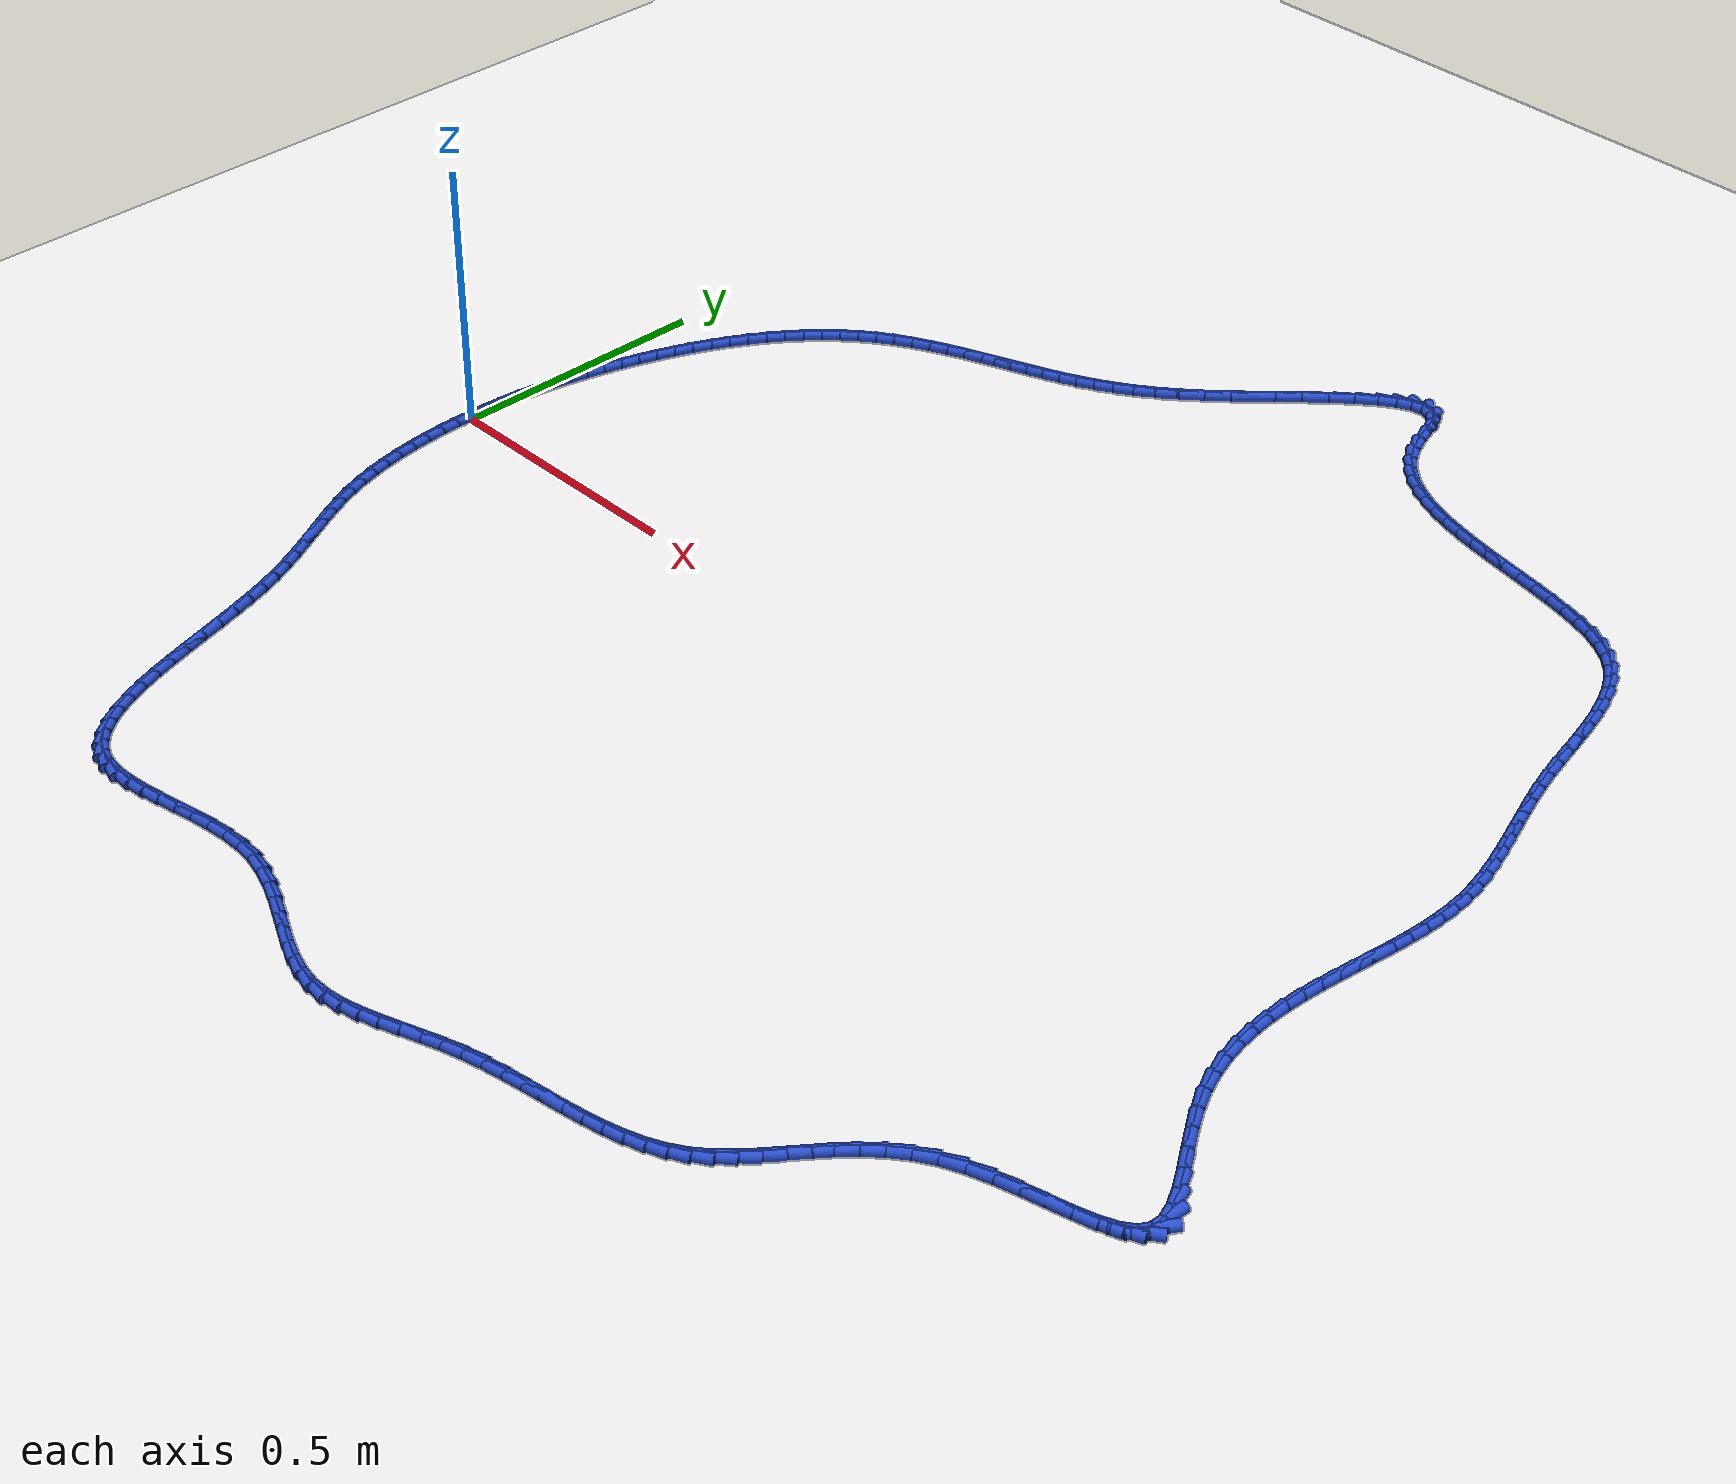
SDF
<sdf version="1.6">
 <world name="default">
  <light name="sun" type="directional">
   <pose>0 0 10 0 -0 0</pose>
   <diffuse>0.8 0.8 0.8 1</diffuse>
   <specular>0.2 0.2 0.2 1</specular>
   <attenuation>
    <range>1000</range>
    <constant>0.9</constant>
    <linear>0.01</linear>
    <quadratic>0.001</quadratic>
   </attenuation>
   <direction>-0.5 0.1 -0.9</direction>
  </light>
  <model name="ground_plane">
   <static>1</static>
   <link name="link">
    <collision name="collision">
     <geometry><plane><normal>0 0 1</normal><size>100 100</size></plane></geometry>
     <surface><friction><ode><mu>100</mu><mu2>50</mu2></ode></friction></surface>
    </collision>
    <visual name="visual">
     <cast_shadows>0</cast_shadows>
     <geometry><plane><normal>0 0 1</normal><size>100 100</size></plane></geometry>
     <material>
      <script><uri>file://media/materials/scripts/gazebo.material</uri><name>Gazebo/WhiteGlow</name></script>
     </material>
    </visual>
   </link>
  </model>
  <gravity>0 0 -9.8</gravity>
  <magnetic_field>6e-06 2.3e-05 -4.2e-05</magnetic_field>
  <atmosphere type="adiabatic"/>
  <physics name="default_physics" default="0" type="ode">
   <max_step_size>0.001</max_step_size>
   <real_time_factor>1</real_time_factor>
   <real_time_update_rate>1000</real_time_update_rate>
  </physics>
  <scene><ambient>0.4 0.4 0.4 1</ambient><background>0.7 0.7 0.7 1</background><shadows>1</shadows></scene>
  <spherical_coordinates>
   <surface_model>EARTH_WGS84</surface_model>
   <latitude_deg>0</latitude_deg>
   <longitude_deg>0</longitude_deg>
   <elevation>0</elevation>
   <heading_deg>0</heading_deg>
  </spherical_coordinates>
  <model name="line">
   <link name="link_0">
    <pose>6.938893903907228e-18 -2.0816681711721685e-17 0.01 0 1.57 1.5395726803142173</pose>
    <collision name="collision">
     <geometry><cylinder><radius>0.01</radius><length>0.08</length></cylinder></geometry>
    </collision>
    <visual name="visual">
     <material>
      <script><name>Gazebo/Blue</name><uri>file://media/materials/scripts/gazebo.material</uri></script>
     </material>
     <geometry><cylinder><radius>0.01</radius><length>0.08</length></cylinder></geometry>
    </visual>
   </link>
   <link name="link_1">
    <pose>0.0010787189975619287 0.034536914896765615 0.01 0 1.57 1.5081255866504448</pose>
    <collision name="collision">
     <geometry><cylinder><radius>0.01</radius><length>0.08</length></cylinder></geometry>
    </collision>
    <visual name="visual">
     <material>
      <script><name>Gazebo/Blue</name><uri>file://media/materials/scripts/gazebo.material</uri></script>
     </material>
     <geometry><cylinder><radius>0.01</radius><length>0.08</length></cylinder></geometry>
    </visual>
   </link>
   <link name="link_2">
    <pose>0.003230668482445049 0.06882933579597644 0.01 0 1.57 1.4767746153901073</pose>
    <collision name="collision">
     <geometry><cylinder><radius>0.01</radius><length>0.08</length></cylinder></geometry>
    </collision>
    <visual name="visual">
     <material>
      <script><name>Gazebo/Blue</name><uri>file://media/materials/scripts/gazebo.material</uri></script>
     </material>
     <geometry><cylinder><radius>0.01</radius><length>0.08</length></cylinder></geometry>
    </visual>
   </link>
   <link name="link_3">
    <pose>0.006444871872062578 0.10291429852605796 0.01 0 1.57 1.445681829038593</pose>
    <collision name="collision">
     <geometry><cylinder><radius>0.01</radius><length>0.08</length></cylinder></geometry>
    </collision>
    <visual name="visual">
     <material>
      <script><name>Gazebo/Blue</name><uri>file://media/materials/scripts/gazebo.material</uri></script>
     </material>
     <geometry><cylinder><radius>0.01</radius><length>0.08</length></cylinder></geometry>
    </visual>
   </link>
   <link name="link_4">
    <pose>0.010710352583827732 0.1368288389154358 0.01 0 1.57 1.4150057100489364</pose>
    <collision name="collision">
     <geometry><cylinder><radius>0.01</radius><length>0.08</length></cylinder></geometry>
    </collision>
    <visual name="visual">
     <material>
      <script><name>Gazebo/Blue</name><uri>file://media/materials/scripts/gazebo.material</uri></script>
     </material>
     <geometry><cylinder><radius>0.01</radius><length>0.08</length></cylinder></geometry>
    </visual>
   </link>
   <link name="link_5">
    <pose>0.01601613403515372 0.1706099927925355 0.01 0 1.57 1.3848976582385846</pose>
    <collision name="collision">
     <geometry><cylinder><radius>0.01</radius><length>0.08</length></cylinder></geometry>
    </collision>
    <visual name="visual">
     <material>
      <script><name>Gazebo/Blue</name><uri>file://media/materials/scripts/gazebo.material</uri></script>
     </material>
     <geometry><cylinder><radius>0.01</radius><length>0.08</length></cylinder></geometry>
    </visual>
   </link>
   <link name="link_6">
    <pose>0.022351239643453754 0.2042947959857826 0.01 0 1.57 1.3554988640223344</pose>
    <collision name="collision">
     <geometry><cylinder><radius>0.01</radius><length>0.08</length></cylinder></geometry>
    </collision>
    <visual name="visual">
     <material>
      <script><name>Gazebo/Blue</name><uri>file://media/materials/scripts/gazebo.material</uri></script>
     </material>
     <geometry><cylinder><radius>0.01</radius><length>0.08</length></cylinder></geometry>
    </visual>
   </link>
   <link name="link_7">
    <pose>0.029704692826141056 0.23792028432360263 0.01 0 1.57 1.3269377060092435</pose>
    <collision name="collision">
     <geometry><cylinder><radius>0.01</radius><length>0.08</length></cylinder></geometry>
    </collision>
    <visual name="visual">
     <material>
      <script><name>Gazebo/Blue</name><uri>file://media/materials/scripts/gazebo.material</uri></script>
     </material>
     <geometry><cylinder><radius>0.01</radius><length>0.08</length></cylinder></geometry>
    </visual>
   </link>
   <link name="link_8">
    <pose>0.03806551700062881 0.27152349363442113 0.01 0 1.57 1.2993137629737328</pose>
    <collision name="collision">
     <geometry><cylinder><radius>0.01</radius><length>0.08</length></cylinder></geometry>
    </collision>
    <visual name="visual">
     <material>
      <script><name>Gazebo/Blue</name><uri>file://media/materials/scripts/gazebo.material</uri></script>
     </material>
     <geometry><cylinder><radius>0.01</radius><length>0.08</length></cylinder></geometry>
    </visual>
   </link>
   <link name="link_9">
    <pose>0.047423001072118345 0.30514059047941017 0.01 0 1.57 1.2716792525355325</pose>
    <collision name="collision">
     <geometry><cylinder><radius>0.01</radius><length>0.08</length></cylinder></geometry>
    </collision>
    <visual name="visual">
     <material>
      <script><name>Gazebo/Blue</name><uri>file://media/materials/scripts/gazebo.material</uri></script>
     </material>
     <geometry><cylinder><radius>0.01</radius><length>0.08</length></cylinder></geometry>
    </visual>
   </link>
   <link name="link_10">
    <pose>0.05778557948021809 0.33874505459624127 0.01 0 1.57 1.2422311300721802</pose>
    <collision name="collision">
     <geometry><cylinder><radius>0.01</radius><length>0.08</length></cylinder></geometry>
    </collision>
    <visual name="visual">
     <material>
      <script><name>Gazebo/Blue</name><uri>file://media/materials/scripts/gazebo.material</uri></script>
     </material>
     <geometry><cylinder><radius>0.01</radius><length>0.08</length></cylinder></geometry>
    </visual>
   </link>
   <link name="link_11">
    <pose>0.069193376139893 0.3722066071903751 0.01 0 1.57 1.2105960277250443</pose>
    <collision name="collision">
     <geometry><cylinder><radius>0.01</radius><length>0.08</length></cylinder></geometry>
    </collision>
    <visual name="visual">
     <material>
      <script><name>Gazebo/Blue</name><uri>file://media/materials/scripts/gazebo.material</uri></script>
     </material>
     <geometry><cylinder><radius>0.01</radius><length>0.08</length></cylinder></geometry>
    </visual>
   </link>
   <link name="link_12">
    <pose>0.08168949071407883 0.4053852261932598 0.01 0 1.57 1.1765427783230729</pose>
    <collision name="collision">
     <geometry><cylinder><radius>0.01</radius><length>0.08</length></cylinder></geometry>
    </collision>
    <visual name="visual">
     <material>
      <script><name>Gazebo/Blue</name><uri>file://media/materials/scripts/gazebo.material</uri></script>
     </material>
     <geometry><cylinder><radius>0.01</radius><length>0.08</length></cylinder></geometry>
    </visual>
   </link>
   <link name="link_13">
    <pose>0.09531702286571156 0.438140889536344 0.01 0 1.57 1.139826450582027</pose>
    <collision name="collision">
     <geometry><cylinder><radius>0.01</radius><length>0.08</length></cylinder></geometry>
    </collision>
    <visual name="visual">
     <material>
      <script><name>Gazebo/Blue</name><uri>file://media/materials/scripts/gazebo.material</uri></script>
     </material>
     <geometry><cylinder><radius>0.01</radius><length>0.08</length></cylinder></geometry>
    </visual>
   </link>
   <link name="link_14">
    <pose>0.110119072257727 0.4703335751510758 0.01 0 1.57 1.1001911912436766</pose>
    <collision name="collision">
     <geometry><cylinder><radius>0.01</radius><length>0.08</length></cylinder></geometry>
    </collision>
    <visual name="visual">
     <material>
      <script><name>Gazebo/Blue</name><uri>file://media/materials/scripts/gazebo.material</uri></script>
     </material>
     <geometry><cylinder><radius>0.01</radius><length>0.08</length></cylinder></geometry>
    </visual>
   </link>
   <link name="link_15">
    <pose>0.126138738553061 0.5018232609689038 0.01 0 1.57 1.057375467120987</pose>
    <collision name="collision">
     <geometry><cylinder><radius>0.01</radius><length>0.08</length></cylinder></geometry>
    </collision>
    <visual name="visual">
     <material>
      <script><name>Gazebo/Blue</name><uri>file://media/materials/scripts/gazebo.material</uri></script>
     </material>
     <geometry><cylinder><radius>0.01</radius><length>0.08</length></cylinder></geometry>
    </visual>
   </link>
   <link name="link_16">
    <pose>0.14341912141464944 0.5324699249212762 0.01 0 1.57 1.0111205116031132</pose>
    <collision name="collision">
     <geometry><cylinder><radius>0.01</radius><length>0.08</length></cylinder></geometry>
    </collision>
    <visual name="visual">
     <material>
      <script><name>Gazebo/Blue</name><uri>file://media/materials/scripts/gazebo.material</uri></script>
     </material>
     <geometry><cylinder><radius>0.01</radius><length>0.08</length></cylinder></geometry>
    </visual>
   </link>
   <link name="link_17">
    <pose>0.16200332050542818 0.5621335449396415 0.01 0 1.57 0.9611828644418535</pose>
    <collision name="collision">
     <geometry><cylinder><radius>0.01</radius><length>0.08</length></cylinder></geometry>
    </collision>
    <visual name="visual">
     <material>
      <script><name>Gazebo/Blue</name><uri>file://media/materials/scripts/gazebo.material</uri></script>
     </material>
     <geometry><cylinder><radius>0.01</radius><length>0.08</length></cylinder></geometry>
    </visual>
   </link>
   <link name="link_18">
    <pose>0.1819344354883331 0.5906740989554479 0.01 0 1.57 0.9073518326601895</pose>
    <collision name="collision">
     <geometry><cylinder><radius>0.01</radius><length>0.08</length></cylinder></geometry>
    </collision>
    <visual name="visual">
     <material>
      <script><name>Gazebo/Blue</name><uri>file://media/materials/scripts/gazebo.material</uri></script>
     </material>
     <geometry><cylinder><radius>0.01</radius><length>0.08</length></cylinder></geometry>
    </visual>
   </link>
   <link name="link_19">
    <pose>0.2032555660263001 0.6179515649001439 0.01 0 1.57 0.8494723688109885</pose>
    <collision name="collision">
     <geometry><cylinder><radius>0.01</radius><length>0.08</length></cylinder></geometry>
    </collision>
    <visual name="visual">
     <material>
      <script><name>Gazebo/Blue</name><uri>file://media/materials/scripts/gazebo.material</uri></script>
     </material>
     <geometry><cylinder><radius>0.01</radius><length>0.08</length></cylinder></geometry>
    </visual>
   </link>
   <link name="link_20">
    <pose>0.22600981178226498 0.643825920705178 0.01 0 1.57 0.7874731082207895</pose>
    <collision name="collision">
     <geometry><cylinder><radius>0.01</radius><length>0.08</length></cylinder></geometry>
    </collision>
    <visual name="visual">
     <material>
      <script><name>Gazebo/Blue</name><uri>file://media/materials/scripts/gazebo.material</uri></script>
     </material>
     <geometry><cylinder><radius>0.01</radius><length>0.08</length></cylinder></geometry>
    </visual>
   </link>
   <link name="link_21">
    <pose>0.2502402724191636 0.6681571443019982 0.01 0 1.57 0.7213980028088065</pose>
    <collision name="collision">
     <geometry><cylinder><radius>0.01</radius><length>0.08</length></cylinder></geometry>
    </collision>
    <visual name="visual">
     <material>
      <script><name>Gazebo/Blue</name><uri>file://media/materials/scripts/gazebo.material</uri></script>
     </material>
     <geometry><cylinder><radius>0.01</radius><length>0.08</length></cylinder></geometry>
    </visual>
   </link>
   <link name="link_22">
    <pose>0.2759900475999318 0.6908052136220529 0.01 0 1.57 0.6514381550738182</pose>
    <collision name="collision">
     <geometry><cylinder><radius>0.01</radius><length>0.08</length></cylinder></geometry>
    </collision>
    <visual name="visual">
     <material>
      <script><name>Gazebo/Blue</name><uri>file://media/materials/scripts/gazebo.material</uri></script>
     </material>
     <geometry><cylinder><radius>0.01</radius><length>0.08</length></cylinder></geometry>
    </visual>
   </link>
   <link name="link_23">
    <pose>0.30330223673515827 0.7116301068440639 0.01 0 1.57 0.5804944052638015</pose>
    <collision name="collision">
     <geometry><cylinder><radius>0.01</radius><length>0.08</length></cylinder></geometry>
    </collision>
    <visual name="visual">
     <material>
      <script><name>Gazebo/Blue</name><uri>file://media/materials/scripts/gazebo.material</uri></script>
     </material>
     <geometry><cylinder><radius>0.01</radius><length>0.08</length></cylinder></geometry>
    </visual>
   </link>
   <link name="link_24">
    <pose>0.33215592537552213 0.7305545286635012 0.01 0 1.57 0.5183572075855268</pose>
    <collision name="collision">
     <geometry><cylinder><radius>0.01</radius><length>0.08</length></cylinder></geometry>
    </collision>
    <visual name="visual">
     <material>
      <script><name>Gazebo/Blue</name><uri>file://media/materials/scripts/gazebo.material</uri></script>
     </material>
     <geometry><cylinder><radius>0.01</radius><length>0.08</length></cylinder></geometry>
    </visual>
   </link>
   <link name="link_25">
    <pose>0.3622861773466556 0.7477402981308431 0.01 0 1.57 0.46683474233749916</pose>
    <collision name="collision">
     <geometry><cylinder><radius>0.01</radius><length>0.08</length></cylinder></geometry>
    </collision>
    <visual name="visual">
     <material>
      <script><name>Gazebo/Blue</name><uri>file://media/materials/scripts/gazebo.material</uri></script>
     </material>
     <geometry><cylinder><radius>0.01</radius><length>0.08</length></cylinder></geometry>
    </visual>
   </link>
   <link name="link_26">
    <pose>0.3933699193604577 0.7634062022507494 0.01 0 1.57 0.42530175828818706</pose>
    <collision name="collision">
     <geometry><cylinder><radius>0.01</radius><length>0.08</length></cylinder></geometry>
    </collision>
    <visual name="visual">
     <material>
      <script><name>Gazebo/Blue</name><uri>file://media/materials/scripts/gazebo.material</uri></script>
     </material>
     <geometry><cylinder><radius>0.01</radius><length>0.08</length></cylinder></geometry>
    </visual>
   </link>
   <link name="link_27">
    <pose>0.42508407812882837 0.7777710280278807 0.01 0 1.57 0.39319994170133654</pose>
    <collision name="collision">
     <geometry><cylinder><radius>0.01</radius><length>0.08</length></cylinder></geometry>
    </collision>
    <visual name="visual">
     <material>
      <script><name>Gazebo/Blue</name><uri>file://media/materials/scripts/gazebo.material</uri></script>
     </material>
     <geometry><cylinder><radius>0.01</radius><length>0.08</length></cylinder></geometry>
    </visual>
   </link>
   <link name="link_28">
    <pose>0.45710558036366666 0.7910535624668967 0.01 0 1.57 0.37014040339746834</pose>
    <collision name="collision">
     <geometry><cylinder><radius>0.01</radius><length>0.08</length></cylinder></geometry>
    </collision>
    <visual name="visual">
     <material>
      <script><name>Gazebo/Blue</name><uri>file://media/materials/scripts/gazebo.material</uri></script>
     </material>
     <geometry><cylinder><radius>0.01</radius><length>0.08</length></cylinder></geometry>
    </visual>
   </link>
   <link name="link_29">
    <pose>0.48911135277687207 0.8034725925724578 0.01 0 1.57 0.3559770471485359</pose>
    <collision name="collision">
     <geometry><cylinder><radius>0.01</radius><length>0.08</length></cylinder></geometry>
    </collision>
    <visual name="visual">
     <material>
      <script><name>Gazebo/Blue</name><uri>file://media/materials/scripts/gazebo.material</uri></script>
     </material>
     <geometry><cylinder><radius>0.01</radius><length>0.08</length></cylinder></geometry>
    </visual>
   </link>
   <link name="link_30">
    <pose>0.5207783220803441 0.8152469053492242 0.01 0 1.57 0.3508688354635092</pose>
    <collision name="collision">
     <geometry><cylinder><radius>0.01</radius><length>0.08</length></cylinder></geometry>
    </collision>
    <visual name="visual">
     <material>
      <script><name>Gazebo/Blue</name><uri>file://media/materials/scripts/gazebo.material</uri></script>
     </material>
     <geometry><cylinder><radius>0.01</radius><length>0.08</length></cylinder></geometry>
    </visual>
   </link>
   <link name="link_31">
    <pose>0.551787324866967 0.8265966162490356 0.01 0 1.57 0.3551749154991921</pose>
    <collision name="collision">
     <geometry><cylinder><radius>0.01</radius><length>0.08</length></cylinder></geometry>
    </collision>
    <visual name="visual">
     <material>
      <script><name>Gazebo/Blue</name><uri>file://media/materials/scripts/gazebo.material</uri></script>
     </material>
     <geometry><cylinder><radius>0.01</radius><length>0.08</length></cylinder></geometry>
    </visual>
   </link>
   <link name="link_32">
    <pose>0.582020876909174 0.8378103645837458 0.01 0 1.57 0.3691811578344682</pose>
    <collision name="collision">
     <geometry><cylinder><radius>0.01</radius><length>0.08</length></cylinder></geometry>
    </collision>
    <visual name="visual">
     <material>
      <script><name>Gazebo/Blue</name><uri>file://media/materials/scripts/gazebo.material</uri></script>
     </material>
     <geometry><cylinder><radius>0.01</radius><length>0.08</length></cylinder></geometry>
    </visual>
   </link>
   <link name="link_33">
    <pose>0.6116565110295054 0.8492770266211908 0.01 0 1.57 0.3928554119733117</pose>
    <collision name="collision">
     <geometry><cylinder><radius>0.01</radius><length>0.08</length></cylinder></geometry>
    </collision>
    <visual name="visual">
     <material>
      <script><name>Gazebo/Blue</name><uri>file://media/materials/scripts/gazebo.material</uri></script>
     </material>
     <geometry><cylinder><radius>0.01</radius><length>0.08</length></cylinder></geometry>
    </visual>
   </link>
   <link name="link_34">
    <pose>0.6408951882540785 0.8613934387515454 0.01 0 1.57 0.42553629461489445</pose>
    <collision name="collision">
     <geometry><cylinder><radius>0.01</radius><length>0.08</length></cylinder></geometry>
    </collision>
    <visual name="visual">
     <material>
      <script><name>Gazebo/Blue</name><uri>file://media/materials/scripts/gazebo.material</uri></script>
     </material>
     <geometry><cylinder><radius>0.01</radius><length>0.08</length></cylinder></geometry>
    </visual>
   </link>
   <link name="link_35">
    <pose>0.669937869609011 0.8745564373649846 0.01 0 1.57 0.46591985496904315</pose>
    <collision name="collision">
     <geometry><cylinder><radius>0.01</radius><length>0.08</length></cylinder></geometry>
    </collision>
    <visual name="visual">
     <material>
      <script><name>Gazebo/Blue</name><uri>file://media/materials/scripts/gazebo.material</uri></script>
     </material>
     <geometry><cylinder><radius>0.01</radius><length>0.08</length></cylinder></geometry>
    </visual>
   </link>
   <link name="link_36">
    <pose>0.6989855161204205 0.8891628588516828 0.01 0 1.57 0.5121699062970289</pose>
    <collision name="collision">
     <geometry><cylinder><radius>0.01</radius><length>0.08</length></cylinder></geometry>
    </collision>
    <visual name="visual">
     <material>
      <script><name>Gazebo/Blue</name><uri>file://media/materials/scripts/gazebo.material</uri></script>
     </material>
     <geometry><cylinder><radius>0.01</radius><length>0.08</length></cylinder></geometry>
    </visual>
   </link>
   <link name="link_37">
    <pose>0.7282390888144248 0.9056095396018154 0.01 0 1.57 0.5621309083754067</pose>
    <collision name="collision">
     <geometry><cylinder><radius>0.01</radius><length>0.08</length></cylinder></geometry>
    </collision>
    <visual name="visual">
     <material>
      <script><name>Gazebo/Blue</name><uri>file://media/materials/scripts/gazebo.material</uri></script>
     </material>
     <geometry><cylinder><radius>0.01</radius><length>0.08</length></cylinder></geometry>
    </visual>
   </link>
   <link name="link_38">
    <pose>0.7578995487171408 0.9242933160055568 0.01 0 1.57 0.6136002810492278</pose>
    <collision name="collision">
     <geometry><cylinder><radius>0.01</radius><length>0.08</length></cylinder></geometry>
    </collision>
    <visual name="visual">
     <material>
      <script><name>Gazebo/Blue</name><uri>file://media/materials/scripts/gazebo.material</uri></script>
     </material>
     <geometry><cylinder><radius>0.01</radius><length>0.08</length></cylinder></geometry>
    </visual>
   </link>
   <link name="link_39">
    <pose>0.7881678568546865 0.9456110244530816 0.01 0 1.57 0.6645898140644212</pose>
    <collision name="collision">
     <geometry><cylinder><radius>0.01</radius><length>0.08</length></cylinder></geometry>
    </collision>
    <visual name="visual">
     <material>
      <script><name>Gazebo/Blue</name><uri>file://media/materials/scripts/gazebo.material</uri></script>
     </material>
     <geometry><cylinder><radius>0.01</radius><length>0.08</length></cylinder></geometry>
    </visual>
   </link>
   <link name="link_40">
    <pose>0.8192449742531794 0.9699595013345648 0.01 0 1.57 0.7134984987689619</pose>
    <collision name="collision">
     <geometry><cylinder><radius>0.01</radius><length>0.08</length></cylinder></geometry>
    </collision>
    <visual name="visual">
     <material>
      <script><name>Gazebo/Blue</name><uri>file://media/materials/scripts/gazebo.material</uri></script>
     </material>
     <geometry><cylinder><radius>0.01</radius><length>0.08</length></cylinder></geometry>
    </visual>
   </link>
   <link name="link_41">
    <pose>0.8513314733616647 0.9977345436793317 0.01 0 1.57 0.7547451613966405</pose>
    <collision name="collision">
     <geometry><cylinder><radius>0.01</radius><length>0.08</length></cylinder></geometry>
    </collision>
    <visual name="visual">
     <material>
      <script><name>Gazebo/Blue</name><uri>file://media/materials/scripts/gazebo.material</uri></script>
     </material>
     <geometry><cylinder><radius>0.01</radius><length>0.08</length></cylinder></geometry>
    </visual>
   </link>
   <link name="link_42">
    <pose>0.8844652569719982 1.0288968418538567 0.01 0 1.57 0.7794222139113126</pose>
    <collision name="collision">
     <geometry><cylinder><radius>0.01</radius><length>0.08</length></cylinder></geometry>
    </collision>
    <visual name="visual">
     <material>
      <script><name>Gazebo/Blue</name><uri>file://media/materials/scripts/gazebo.material</uri></script>
     </material>
     <geometry><cylinder><radius>0.01</radius><length>0.08</length></cylinder></geometry>
    </visual>
   </link>
   <link name="link_43">
    <pose>0.9182704947264925 1.062300438229421 0.01 0 1.57 0.7896335143248391</pose>
    <collision name="collision">
     <geometry><cylinder><radius>0.01</radius><length>0.08</length></cylinder></geometry>
    </collision>
    <visual name="visual">
     <material>
      <script><name>Gazebo/Blue</name><uri>file://media/materials/scripts/gazebo.material</uri></script>
     </material>
     <geometry><cylinder><radius>0.01</radius><length>0.08</length></cylinder></geometry>
    </visual>
   </link>
   <link name="link_44">
    <pose>0.9523065491469905 1.0966260299425301 0.01 0 1.57 0.7869043434274262</pose>
    <collision name="collision">
     <geometry><cylinder><radius>0.01</radius><length>0.08</length></cylinder></geometry>
    </collision>
    <visual name="visual">
     <material>
      <script><name>Gazebo/Blue</name><uri>file://media/materials/scripts/gazebo.material</uri></script>
     </material>
     <geometry><cylinder><radius>0.01</radius><length>0.08</length></cylinder></geometry>
    </visual>
   </link>
   <link name="link_45">
    <pose>0.9861327827553367 1.1305543141296905 0.01 0 1.57 0.7706547886719611</pose>
    <collision name="collision">
     <geometry><cylinder><radius>0.01</radius><length>0.08</length></cylinder></geometry>
    </collision>
    <visual name="visual">
     <material>
      <script><name>Gazebo/Blue</name><uri>file://media/materials/scripts/gazebo.material</uri></script>
     </material>
     <geometry><cylinder><radius>0.01</radius><length>0.08</length></cylinder></geometry>
    </visual>
   </link>
   <link name="link_46">
    <pose>1.0193085580733734 1.1627659879274077 0.01 0 1.57 0.7379493426746008</pose>
    <collision name="collision">
     <geometry><cylinder><radius>0.01</radius><length>0.08</length></cylinder></geometry>
    </collision>
    <visual name="visual">
     <material>
      <script><name>Gazebo/Blue</name><uri>file://media/materials/scripts/gazebo.material</uri></script>
     </material>
     <geometry><cylinder><radius>0.01</radius><length>0.08</length></cylinder></geometry>
    </visual>
   </link>
   <link name="link_47">
    <pose>1.0513932376229451 1.1919417484721886 0.01 0 1.57 0.6822431229085715</pose>
    <collision name="collision">
     <geometry><cylinder><radius>0.01</radius><length>0.08</length></cylinder></geometry>
    </collision>
    <visual name="visual">
     <material>
      <script><name>Gazebo/Blue</name><uri>file://media/materials/scripts/gazebo.material</uri></script>
     </material>
     <geometry><cylinder><radius>0.01</radius><length>0.08</length></cylinder></geometry>
    </visual>
   </link>
   <link name="link_48">
    <pose>1.0819461839258948 1.2167622929005386 0.01 0 1.57 0.5902352593134981</pose>
    <collision name="collision">
     <geometry><cylinder><radius>0.01</radius><length>0.08</length></cylinder></geometry>
    </collision>
    <visual name="visual">
     <material>
      <script><name>Gazebo/Blue</name><uri>file://media/materials/scripts/gazebo.material</uri></script>
     </material>
     <geometry><cylinder><radius>0.01</radius><length>0.08</length></cylinder></geometry>
    </visual>
   </link>
   <link name="link_49">
    <pose>1.110526759504066 1.2359083183489639 0.01 0 1.57 0.43476376833054675</pose>
    <collision name="collision">
     <geometry><cylinder><radius>0.01</radius><length>0.08</length></cylinder></geometry>
    </collision>
    <visual name="visual">
     <material>
      <script><name>Gazebo/Blue</name><uri>file://media/materials/scripts/gazebo.material</uri></script>
     </material>
     <geometry><cylinder><radius>0.01</radius><length>0.08</length></cylinder></geometry>
    </visual>
   </link>
   <link name="link_50">
    <pose>1.1366943268793017 1.2480605219539709 0.01 0 1.57 0.1632043211630677</pose>
    <collision name="collision">
     <geometry><cylinder><radius>0.01</radius><length>0.08</length></cylinder></geometry>
    </collision>
    <visual name="visual">
     <material>
      <script><name>Gazebo/Blue</name><uri>file://media/materials/scripts/gazebo.material</uri></script>
     </material>
     <geometry><cylinder><radius>0.01</radius><length>0.08</length></cylinder></geometry>
    </visual>
   </link>
   <link name="link_51">
    <pose>1.1600082485734464 1.2518996008520658 0.01 0 1.57 -0.28168845116691477</pose>
    <collision name="collision">
     <geometry><cylinder><radius>0.01</radius><length>0.08</length></cylinder></geometry>
    </collision>
    <visual name="visual">
     <material>
      <script><name>Gazebo/Blue</name><uri>file://media/materials/scripts/gazebo.material</uri></script>
     </material>
     <geometry><cylinder><radius>0.01</radius><length>0.08</length></cylinder></geometry>
    </visual>
   </link>
   <link name="link_52">
    <pose>1.1800278871083427 1.2461062521797537 0.01 0 1.57 -0.7993350156907365</pose>
    <collision name="collision">
     <geometry><cylinder><radius>0.01</radius><length>0.08</length></cylinder></geometry>
    </collision>
    <visual name="visual">
     <material>
      <script><name>Gazebo/Blue</name><uri>file://media/materials/scripts/gazebo.material</uri></script>
     </material>
     <geometry><cylinder><radius>0.01</radius><length>0.08</length></cylinder></geometry>
    </visual>
   </link>
   <link name="link_53">
    <pose>1.1963126050058341 1.2293611730735412 0.01 0 1.57 -1.1512723161892442</pose>
    <collision name="collision">
     <geometry><cylinder><radius>0.01</radius><length>0.08</length></cylinder></geometry>
    </collision>
    <visual name="visual">
     <material>
      <script><name>Gazebo/Blue</name><uri>file://media/materials/scripts/gazebo.material</uri></script>
     </material>
     <geometry><cylinder><radius>0.01</radius><length>0.08</length></cylinder></geometry>
    </visual>
   </link>
   <link name="link_54">
    <pose>1.2088474479087175 1.2012562546108616 0.01 0 1.57 -1.2470230080012707</pose>
    <collision name="collision">
     <geometry><cylinder><radius>0.01</radius><length>0.08</length></cylinder></geometry>
    </collision>
    <visual name="visual">
     <material>
      <script><name>Gazebo/Blue</name><uri>file://media/materials/scripts/gazebo.material</uri></script>
     </material>
     <geometry><cylinder><radius>0.01</radius><length>0.08</length></cylinder></geometry>
    </visual>
   </link>
   <link name="link_55">
    <pose>1.2203006594684038 1.167126894358867 0.01 0 1.57 -1.170710706884832</pose>
    <collision name="collision">
     <geometry><cylinder><radius>0.01</radius><length>0.08</length></cylinder></geometry>
    </collision>
    <visual name="visual">
     <material>
      <script><name>Gazebo/Blue</name><uri>file://media/materials/scripts/gazebo.material</uri></script>
     </material>
     <geometry><cylinder><radius>0.01</radius><length>0.08</length></cylinder></geometry>
    </visual>
   </link>
   <link name="link_56">
    <pose>1.2342181811908284 1.1342167162110688 0.01 0 1.57 -1.020286848414421</pose>
    <collision name="collision">
     <geometry><cylinder><radius>0.01</radius><length>0.08</length></cylinder></geometry>
    </collision>
    <visual name="visual">
     <material>
      <script><name>Gazebo/Blue</name><uri>file://media/materials/scripts/gazebo.material</uri></script>
     </material>
     <geometry><cylinder><radius>0.01</radius><length>0.08</length></cylinder></geometry>
    </visual>
   </link>
   <link name="link_57">
    <pose>1.2519129534556381 1.1053887802179643 0.01 0 1.57 -0.8687714558804847</pose>
    <collision name="collision">
     <geometry><cylinder><radius>0.01</radius><length>0.08</length></cylinder></geometry>
    </collision>
    <visual name="visual">
     <material>
      <script><name>Gazebo/Blue</name><uri>file://media/materials/scripts/gazebo.material</uri></script>
     </material>
     <geometry><cylinder><radius>0.01</radius><length>0.08</length></cylinder></geometry>
    </visual>
   </link>
   <link name="link_58">
    <pose>1.27308937787317 1.0803503157168026 0.01 0 1.57 -0.7263460380362501</pose>
    <collision name="collision">
     <geometry><cylinder><radius>0.01</radius><length>0.08</length></cylinder></geometry>
    </collision>
    <visual name="visual">
     <material>
      <script><name>Gazebo/Blue</name><uri>file://media/materials/scripts/gazebo.material</uri></script>
     </material>
     <geometry><cylinder><radius>0.01</radius><length>0.08</length></cylinder></geometry>
    </visual>
   </link>
   <link name="link_59">
    <pose>1.297416472338468 1.0587391318868649 0.01 0 1.57 -0.5993468259165707</pose>
    <collision name="collision">
     <geometry><cylinder><radius>0.01</radius><length>0.08</length></cylinder></geometry>
    </collision>
    <visual name="visual">
     <material>
      <script><name>Gazebo/Blue</name><uri>file://media/materials/scripts/gazebo.material</uri></script>
     </material>
     <geometry><cylinder><radius>0.01</radius><length>0.08</length></cylinder></geometry>
    </visual>
   </link>
   <link name="link_60">
    <pose>1.3245632547465773 1.0401930379074333 0.01 0 1.57 -0.4909446182707565</pose>
    <collision name="collision">
     <geometry><cylinder><radius>0.01</radius><length>0.08</length></cylinder></geometry>
    </collision>
    <visual name="visual">
     <material>
      <script><name>Gazebo/Blue</name><uri>file://media/materials/scripts/gazebo.material</uri></script>
     </material>
     <geometry><cylinder><radius>0.01</radius><length>0.08</length></cylinder></geometry>
    </visual>
   </link>
   <link name="link_61">
    <pose>1.3541987429925422 1.02434984295779 0.01 0 1.57 -0.4016141087658761</pose>
    <collision name="collision">
     <geometry><cylinder><radius>0.01</radius><length>0.08</length></cylinder></geometry>
    </collision>
    <visual name="visual">
     <material>
      <script><name>Gazebo/Blue</name><uri>file://media/materials/scripts/gazebo.material</uri></script>
     </material>
     <geometry><cylinder><radius>0.01</radius><length>0.08</length></cylinder></geometry>
    </visual>
   </link>
   <link name="link_62">
    <pose>1.3859919549714088 1.0108473562172167 0.01 0 1.57 -0.33022091602826725</pose>
    <collision name="collision">
     <geometry><cylinder><radius>0.01</radius><length>0.08</length></cylinder></geometry>
    </collision>
    <visual name="visual">
     <material>
      <script><name>Gazebo/Blue</name><uri>file://media/materials/scripts/gazebo.material</uri></script>
     </material>
     <geometry><cylinder><radius>0.01</radius><length>0.08</length></cylinder></geometry>
    </visual>
   </link>
   <link name="link_63">
    <pose>1.4196119085782217 0.999323386864995 0.01 0 1.57 -0.2749945384267629</pose>
    <collision name="collision">
     <geometry><cylinder><radius>0.01</radius><length>0.08</length></cylinder></geometry>
    </collision>
    <visual name="visual">
     <material>
      <script><name>Gazebo/Blue</name><uri>file://media/materials/scripts/gazebo.material</uri></script>
     </material>
     <geometry><cylinder><radius>0.01</radius><length>0.08</length></cylinder></geometry>
    </visual>
   </link>
   <link name="link_64">
    <pose>1.4547276217080256 0.9894157440804076 0.01 0 1.57 -0.23414210269544694</pose>
    <collision name="collision">
     <geometry><cylinder><radius>0.01</radius><length>0.08</length></cylinder></geometry>
    </collision>
    <visual name="visual">
     <material>
      <script><name>Gazebo/Blue</name><uri>file://media/materials/scripts/gazebo.material</uri></script>
     </material>
     <geometry><cylinder><radius>0.01</radius><length>0.08</length></cylinder></geometry>
    </visual>
   </link>
   <link name="link_65">
    <pose>1.4910081122558652 0.9807622370427358 0.01 0 1.57 -0.20615496180572326</pose>
    <collision name="collision">
     <geometry><cylinder><radius>0.01</radius><length>0.08</length></cylinder></geometry>
    </collision>
    <visual name="visual">
     <material>
      <script><name>Gazebo/Blue</name><uri>file://media/materials/scripts/gazebo.material</uri></script>
     </material>
     <geometry><cylinder><radius>0.01</radius><length>0.08</length></cylinder></geometry>
    </visual>
   </link>
   <link name="link_66">
    <pose>1.528122398116786 0.9730006749312611 0.01 0 1.57 -0.18993061982486512</pose>
    <collision name="collision">
     <geometry><cylinder><radius>0.01</radius><length>0.08</length></cylinder></geometry>
    </collision>
    <visual name="visual">
     <material>
      <script><name>Gazebo/Blue</name><uri>file://media/materials/scripts/gazebo.material</uri></script>
     </material>
     <geometry><cylinder><radius>0.01</radius><length>0.08</length></cylinder></geometry>
    </visual>
   </link>
   <link name="link_67">
    <pose>1.5657394971858325 0.9657688669252662 0.01 0 1.57 -0.18480645672734122</pose>
    <collision name="collision">
     <geometry><cylinder><radius>0.01</radius><length>0.08</length></cylinder></geometry>
    </collision>
    <visual name="visual">
     <material>
      <script><name>Gazebo/Blue</name><uri>file://media/materials/scripts/gazebo.material</uri></script>
     </material>
     <geometry><cylinder><radius>0.01</radius><length>0.08</length></cylinder></geometry>
    </visual>
   </link>
   <link name="link_68">
    <pose>1.60352842735805 0.9587046222040325 0.01 0 1.57 -0.1905616601111022</pose>
    <collision name="collision">
     <geometry><cylinder><radius>0.01</radius><length>0.08</length></cylinder></geometry>
    </collision>
    <visual name="visual">
     <material>
      <script><name>Gazebo/Blue</name><uri>file://media/materials/scripts/gazebo.material</uri></script>
     </material>
     <geometry><cylinder><radius>0.01</radius><length>0.08</length></cylinder></geometry>
    </visual>
   </link>
   <link name="link_69">
    <pose>1.6411582065284833 0.951445749946842 0.01 0 1.57 -0.20741417829386574</pose>
    <collision name="collision">
     <geometry><cylinder><radius>0.01</radius><length>0.08</length></cylinder></geometry>
    </collision>
    <visual name="visual">
     <material>
      <script><name>Gazebo/Blue</name><uri>file://media/materials/scripts/gazebo.material</uri></script>
     </material>
     <geometry><cylinder><radius>0.01</radius><length>0.08</length></cylinder></geometry>
    </visual>
   </link>
   <link name="link_70">
    <pose>1.678297852592178 0.9436300593329772 0.01 0 1.57 -0.23604567205010119</pose>
    <collision name="collision">
     <geometry><cylinder><radius>0.01</radius><length>0.08</length></cylinder></geometry>
    </collision>
    <visual name="visual">
     <material>
      <script><name>Gazebo/Blue</name><uri>file://media/materials/scripts/gazebo.material</uri></script>
     </material>
     <geometry><cylinder><radius>0.01</radius><length>0.08</length></cylinder></geometry>
    </visual>
   </link>
   <link name="link_71">
    <pose>1.7146153330380787 0.9348946304759581 0.01 0 1.57 -0.2807157546478752</pose>
    <collision name="collision">
     <geometry><cylinder><radius>0.01</radius><length>0.08</length></cylinder></geometry>
    </collision>
    <visual name="visual">
     <material>
      <script><name>Gazebo/Blue</name><uri>file://media/materials/scripts/gazebo.material</uri></script>
     </material>
     <geometry><cylinder><radius>0.01</radius><length>0.08</length></cylinder></geometry>
    </visual>
   </link>
   <link name="link_72">
    <pose>1.7496559353815317 0.9247913937854075 0.01 0 1.57 -0.35027326022431576</pose>
    <collision name="collision">
     <geometry><cylinder><radius>0.01</radius><length>0.08</length></cylinder></geometry>
    </collision>
    <visual name="visual">
     <material>
      <script><name>Gazebo/Blue</name><uri>file://media/materials/scripts/gazebo.material</uri></script>
     </material>
     <geometry><cylinder><radius>0.01</radius><length>0.08</length></cylinder></geometry>
    </visual>
   </link>
   <link name="link_73">
    <pose>1.7827290250065377 0.9127085308614429 0.01 0 1.57 -0.450366587782036</pose>
    <collision name="collision">
     <geometry><cylinder><radius>0.01</radius><length>0.08</length></cylinder></geometry>
    </collision>
    <visual name="visual">
     <material>
      <script><name>Gazebo/Blue</name><uri>file://media/materials/scripts/gazebo.material</uri></script>
     </material>
     <geometry><cylinder><radius>0.01</radius><length>0.08</length></cylinder></geometry>
    </visual>
   </link>
   <link name="link_74">
    <pose>1.8131171851819345 0.8980156343763492 0.01 0 1.57 -0.5865335939904592</pose>
    <collision name="collision">
     <geometry><cylinder><radius>0.01</radius><length>0.08</length></cylinder></geometry>
    </collision>
    <visual name="visual">
     <material>
      <script><name>Gazebo/Blue</name><uri>file://media/materials/scripts/gazebo.material</uri></script>
     </material>
     <geometry><cylinder><radius>0.01</radius><length>0.08</length></cylinder></geometry>
    </visual>
   </link>
   <link name="link_75">
    <pose>1.8401029991765587 0.8800822970024091 0.01 0 1.57 -0.7551102985365309</pose>
    <collision name="collision">
     <geometry><cylinder><radius>0.01</radius><length>0.08</length></cylinder></geometry>
    </collision>
    <visual name="visual">
     <material>
      <script><name>Gazebo/Blue</name><uri>file://media/materials/scripts/gazebo.material</uri></script>
     </material>
     <geometry><cylinder><radius>0.01</radius><length>0.08</length></cylinder></geometry>
    </visual>
   </link>
   <link name="link_76">
    <pose>1.863123930709332 0.8584152819881397 0.01 0 1.57 -0.916178957604789</pose>
    <collision name="collision">
     <geometry><cylinder><radius>0.01</radius><length>0.08</length></cylinder></geometry>
    </collision>
    <visual name="visual">
     <material>
      <script><name>Gazebo/Blue</name><uri>file://media/materials/scripts/gazebo.material</uri></script>
     </material>
     <geometry><cylinder><radius>0.01</radius><length>0.08</length></cylinder></geometry>
    </visual>
   </link>
   <link name="link_77">
    <pose>1.8824392841267459 0.8332492194780702 0.01 0 1.57 -1.050793132851884</pose>
    <collision name="collision">
     <geometry><cylinder><radius>0.01</radius><length>0.08</length></cylinder></geometry>
    </collision>
    <visual name="visual">
     <material>
      <script><name>Gazebo/Blue</name><uri>file://media/materials/scripts/gazebo.material</uri></script>
     </material>
     <geometry><cylinder><radius>0.01</radius><length>0.08</length></cylinder></geometry>
    </visual>
   </link>
   <link name="link_78">
    <pose>1.8985799115584474 0.8050592371480175 0.01 0 1.57 -1.1570547523777324</pose>
    <collision name="collision">
     <geometry><cylinder><radius>0.01</radius><length>0.08</length></cylinder></geometry>
    </collision>
    <visual name="visual">
     <material>
      <script><name>Gazebo/Blue</name><uri>file://media/materials/scripts/gazebo.material</uri></script>
     </material>
     <geometry><cylinder><radius>0.01</radius><length>0.08</length></cylinder></geometry>
    </visual>
   </link>
   <link name="link_79">
    <pose>1.912076836443678 0.7743206143949226 0.01 0 1.57 -1.2368377543593658</pose>
    <collision name="collision">
     <geometry><cylinder><radius>0.01</radius><length>0.08</length></cylinder></geometry>
    </collision>
    <visual name="visual">
     <material>
      <script><name>Gazebo/Blue</name><uri>file://media/materials/scripts/gazebo.material</uri></script>
     </material>
     <geometry><cylinder><radius>0.01</radius><length>0.08</length></cylinder></geometry>
    </visual>
   </link>
   <link name="link_80">
    <pose>1.9234610822216767 0.7415086306157266 0.01 0 1.57 -1.2932721722002283</pose>
    <collision name="collision">
     <geometry><cylinder><radius>0.01</radius><length>0.08</length></cylinder></geometry>
    </collision>
    <visual name="visual">
     <material>
      <script><name>Gazebo/Blue</name><uri>file://media/materials/scripts/gazebo.material</uri></script>
     </material>
     <geometry><cylinder><radius>0.01</radius><length>0.08</length></cylinder></geometry>
    </visual>
   </link>
   <link name="link_81">
    <pose>1.9332636723316874 0.7070985652073702 0.01 0 1.57 -1.3292973963451062</pose>
    <collision name="collision">
     <geometry><cylinder><radius>0.01</radius><length>0.08</length></cylinder></geometry>
    </collision>
    <visual name="visual">
     <material>
      <script><name>Gazebo/Blue</name><uri>file://media/materials/scripts/gazebo.material</uri></script>
     </material>
     <geometry><cylinder><radius>0.01</radius><length>0.08</length></cylinder></geometry>
    </visual>
   </link>
   <link name="link_82">
    <pose>1.94201563021295 0.6715656975667935 0.01 0 1.57 -1.3470691940154367</pose>
    <collision name="collision">
     <geometry><cylinder><radius>0.01</radius><length>0.08</length></cylinder></geometry>
    </collision>
    <visual name="visual">
     <material>
      <script><name>Gazebo/Blue</name><uri>file://media/materials/scripts/gazebo.material</uri></script>
     </material>
     <geometry><cylinder><radius>0.01</radius><length>0.08</length></cylinder></geometry>
    </visual>
   </link>
   <link name="link_83">
    <pose>1.9502479793047063 0.6353853070909382 0.01 0 1.57 -1.3477957997203838</pose>
    <collision name="collision">
     <geometry><cylinder><radius>0.01</radius><length>0.08</length></cylinder></geometry>
    </collision>
    <visual name="visual">
     <material>
      <script><name>Gazebo/Blue</name><uri>file://media/materials/scripts/gazebo.material</uri></script>
     </material>
     <geometry><cylinder><radius>0.01</radius><length>0.08</length></cylinder></geometry>
    </visual>
   </link>
   <link name="link_84">
    <pose>1.9584917430461963 0.5990326731767445 0.01 0 1.57 -1.331731854521824</pose>
    <collision name="collision">
     <geometry><cylinder><radius>0.01</radius><length>0.08</length></cylinder></geometry>
    </collision>
    <visual name="visual">
     <material>
      <script><name>Gazebo/Blue</name><uri>file://media/materials/scripts/gazebo.material</uri></script>
     </material>
     <geometry><cylinder><radius>0.01</radius><length>0.08</length></cylinder></geometry>
    </visual>
   </link>
   <link name="link_85">
    <pose>1.9672779448766622 0.5629830752211528 0.01 0 1.57 -1.29977069658318</pose>
    <collision name="collision">
     <geometry><cylinder><radius>0.01</radius><length>0.08</length></cylinder></geometry>
    </collision>
    <visual name="visual">
     <material>
      <script><name>Gazebo/Blue</name><uri>file://media/materials/scripts/gazebo.material</uri></script>
     </material>
     <geometry><cylinder><radius>0.01</radius><length>0.08</length></cylinder></geometry>
    </visual>
   </link>
   <link name="link_86">
    <pose>1.9770876504299142 0.5276789205614197 0.01 0 1.57 -1.2676601633554787</pose>
    <collision name="collision">
     <geometry><cylinder><radius>0.01</radius><length>0.08</length></cylinder></geometry>
    </collision>
    <visual name="visual">
     <material>
      <script><name>Gazebo/Blue</name><uri>file://media/materials/scripts/gazebo.material</uri></script>
     </material>
     <geometry><cylinder><radius>0.01</radius><length>0.08</length></cylinder></geometry>
    </visual>
   </link>
   <link name="link_87">
    <pose>1.9878682416577935 0.4932114545553059 0.01 0 1.57 -1.2457183650536767</pose>
    <collision name="collision">
     <geometry><cylinder><radius>0.01</radius><length>0.08</length></cylinder></geometry>
    </collision>
    <visual name="visual">
     <material>
      <script><name>Gazebo/Blue</name><uri>file://media/materials/scripts/gazebo.material</uri></script>
     </material>
     <geometry><cylinder><radius>0.01</radius><length>0.08</length></cylinder></geometry>
    </visual>
   </link>
   <link name="link_88">
    <pose>1.999243899049323 0.45945925713853647 0.01 0 1.57 -1.2345532991124186</pose>
    <collision name="collision">
     <geometry><cylinder><radius>0.01</radius><length>0.08</length></cylinder></geometry>
    </collision>
    <visual name="visual">
     <material>
      <script><name>Gazebo/Blue</name><uri>file://media/materials/scripts/gazebo.material</uri></script>
     </material>
     <geometry><cylinder><radius>0.01</radius><length>0.08</length></cylinder></geometry>
    </visual>
   </link>
   <link name="link_89">
    <pose>2.010834290094236 0.4262979387092297 0.01 0 1.57 -1.234622903365785</pose>
    <collision name="collision">
     <geometry><cylinder><radius>0.01</radius><length>0.08</length></cylinder></geometry>
    </collision>
    <visual name="visual">
     <material>
      <script><name>Gazebo/Blue</name><uri>file://media/materials/scripts/gazebo.material</uri></script>
     </material>
     <geometry><cylinder><radius>0.01</radius><length>0.08</length></cylinder></geometry>
    </visual>
   </link>
   <link name="link_90">
    <pose>2.0222590822822646 0.39360310966550266 0.01 0 1.57 -1.2464159751977668</pose>
    <collision name="collision">
     <geometry><cylinder><radius>0.01</radius><length>0.08</length></cylinder></geometry>
    </collision>
    <visual name="visual">
     <material>
      <script><name>Gazebo/Blue</name><uri>file://media/materials/scripts/gazebo.material</uri></script>
     </material>
     <geometry><cylinder><radius>0.01</radius><length>0.08</length></cylinder></geometry>
    </visual>
   </link>
   <link name="link_91">
    <pose>2.0331379431031413 0.3612503804054729 0.01 0 1.57 -1.2704535439009121</pose>
    <collision name="collision">
     <geometry><cylinder><radius>0.01</radius><length>0.08</length></cylinder></geometry>
    </collision>
    <visual name="visual">
     <material>
      <script><name>Gazebo/Blue</name><uri>file://media/materials/scripts/gazebo.material</uri></script>
     </material>
     <geometry><cylinder><radius>0.01</radius><length>0.08</length></cylinder></geometry>
    </visual>
   </link>
   <link name="link_92">
    <pose>2.043090540046598 0.3291153613272576 0.01 0 1.57 -1.3072374484816018</pose>
    <collision name="collision">
     <geometry><cylinder><radius>0.01</radius><length>0.08</length></cylinder></geometry>
    </collision>
    <visual name="visual">
     <material>
      <script><name>Gazebo/Blue</name><uri>file://media/materials/scripts/gazebo.material</uri></script>
     </material>
     <geometry><cylinder><radius>0.01</radius><length>0.08</length></cylinder></geometry>
    </visual>
   </link>
   <link name="link_93">
    <pose>2.051736540602368 0.29707366282897507 0.01 0 1.57 -1.3571307263361765</pose>
    <collision name="collision">
     <geometry><cylinder><radius>0.01</radius><length>0.08</length></cylinder></geometry>
    </collision>
    <visual name="visual">
     <material>
      <script><name>Gazebo/Blue</name><uri>file://media/materials/scripts/gazebo.material</uri></script>
     </material>
     <geometry><cylinder><radius>0.01</radius><length>0.08</length></cylinder></geometry>
    </visual>
   </link>
   <link name="link_94">
    <pose>2.0586956122601823 0.2650008953087424 0.01 0 1.57 -1.4201596322199292</pose>
    <collision name="collision">
     <geometry><cylinder><radius>0.01</radius><length>0.08</length></cylinder></geometry>
    </collision>
    <visual name="visual">
     <material>
      <script><name>Gazebo/Blue</name><uri>file://media/materials/scripts/gazebo.material</uri></script>
     </material>
     <geometry><cylinder><radius>0.01</radius><length>0.08</length></cylinder></geometry>
    </visual>
   </link>
   <link name="link_95">
    <pose>2.0635874225097757 0.23277266916467665 0.01 0 1.57 -1.4928342668204582</pose>
    <collision name="collision">
     <geometry><cylinder><radius>0.01</radius><length>0.08</length></cylinder></geometry>
    </collision>
    <visual name="visual">
     <material>
      <script><name>Gazebo/Blue</name><uri>file://media/materials/scripts/gazebo.material</uri></script>
     </material>
     <geometry><cylinder><radius>0.01</radius><length>0.08</length></cylinder></geometry>
    </visual>
   </link>
   <link name="link_96">
    <pose>2.0661256435332356 0.20028152624891563 0.01 0 1.57 -1.5585812397386785</pose>
    <collision name="collision">
     <geometry><cylinder><radius>0.01</radius><length>0.08</length></cylinder></geometry>
    </collision>
    <visual name="visual">
     <material>
      <script><name>Gazebo/Blue</name><uri>file://media/materials/scripts/gazebo.material</uri></script>
     </material>
     <geometry><cylinder><radius>0.01</radius><length>0.08</length></cylinder></geometry>
    </visual>
   </link>
   <link name="link_97">
    <pose>2.0665259652586743 0.16751042826573936 0.01 0 1.57 1.5298062863378659</pose>
    <collision name="collision">
     <geometry><cylinder><radius>0.01</radius><length>0.08</length></cylinder></geometry>
    </collision>
    <visual name="visual">
     <material>
      <script><name>Gazebo/Blue</name><uri>file://media/materials/scripts/gazebo.material</uri></script>
     </material>
     <geometry><cylinder><radius>0.01</radius><length>0.08</length></cylinder></geometry>
    </visual>
   </link>
   <link name="link_98">
    <pose>2.0651709760783117 0.13447239747917347 0.01 0 1.57 1.489049129070172</pose>
    <collision name="collision">
     <geometry><cylinder><radius>0.01</radius><length>0.08</length></cylinder></geometry>
    </collision>
    <visual name="visual">
     <material>
      <script><name>Gazebo/Blue</name><uri>file://media/materials/scripts/gazebo.material</uri></script>
     </material>
     <geometry><cylinder><radius>0.01</radius><length>0.08</length></cylinder></geometry>
    </visual>
   </link>
   <link name="link_99">
    <pose>2.062443376283726 0.10118047630775792 0.01 0 1.57 1.4603851777056263</pose>
    <collision name="collision">
     <geometry><cylinder><radius>0.01</radius><length>0.08</length></cylinder></geometry>
    </collision>
    <visual name="visual">
     <material>
      <script><name>Gazebo/Blue</name><uri>file://media/materials/scripts/gazebo.material</uri></script>
     </material>
     <geometry><cylinder><radius>0.01</radius><length>0.08</length></cylinder></geometry>
    </visual>
   </link>
   <link name="link_100">
    <pose>2.0587258661664927 0.06764770717003178 0.01 0 1.57 1.443390474096842</pose>
    <collision name="collision">
     <geometry><cylinder><radius>0.01</radius><length>0.08</length></cylinder></geometry>
    </collision>
    <visual name="visual">
     <material>
      <script><name>Gazebo/Blue</name><uri>file://media/materials/scripts/gazebo.material</uri></script>
     </material>
     <geometry><cylinder><radius>0.01</radius><length>0.08</length></cylinder></geometry>
    </visual>
   </link>
   <link name="link_101">
    <pose>2.0544011460181895 0.03388713248453381 0.01 0 1.57 1.4376900290612884</pose>
    <collision name="collision">
     <geometry><cylinder><radius>0.01</radius><length>0.08</length></cylinder></geometry>
    </collision>
    <visual name="visual">
     <material>
      <script><name>Gazebo/Blue</name><uri>file://media/materials/scripts/gazebo.material</uri></script>
     </material>
     <geometry><cylinder><radius>0.01</radius><length>0.08</length></cylinder></geometry>
    </visual>
   </link>
   <link name="link_102">
    <pose>2.0498519161303954 -8.820533019580565e-05 0.01 0 1.57 1.4430171899312614</pose>
    <collision name="collision">
     <geometry><cylinder><radius>0.01</radius><length>0.08</length></cylinder></geometry>
    </collision>
    <visual name="visual">
     <material>
      <script><name>Gazebo/Blue</name><uri>file://media/materials/scripts/gazebo.material</uri></script>
     </material>
     <geometry><cylinder><radius>0.01</radius><length>0.08</length></cylinder></geometry>
    </visual>
   </link>
   <link name="link_103">
    <pose>2.045460876794685 -0.03426526385561823 0.01 0 1.57 1.4592270601832764</pose>
    <collision name="collision">
     <geometry><cylinder><radius>0.01</radius><length>0.08</length></cylinder></geometry>
    </collision>
    <visual name="visual">
     <material>
      <script><name>Gazebo/Blue</name><uri>file://media/materials/scripts/gazebo.material</uri></script>
     </material>
     <geometry><cylinder><radius>0.01</radius><length>0.08</length></cylinder></geometry>
    </visual>
   </link>
   <link name="link_104">
    <pose>2.0416107283026363 -0.06863100067319416 0.01 0 1.57 1.4862720489760544</pose>
    <collision name="collision">
     <geometry><cylinder><radius>0.01</radius><length>0.08</length></cylinder></geometry>
    </collision>
    <visual name="visual">
     <material>
      <script><name>Gazebo/Blue</name><uri>file://media/materials/scripts/gazebo.material</uri></script>
     </material>
     <geometry><cylinder><radius>0.01</radius><length>0.08</length></cylinder></geometry>
    </visual>
   </link>
   <link name="link_105">
    <pose>2.0386841709458277 -0.1031723733643843 0.01 0 1.57 1.5241419996947303</pose>
    <collision name="collision">
     <geometry><cylinder><radius>0.01</radius><length>0.08</length></cylinder></geometry>
    </collision>
    <visual name="visual">
     <material>
      <script><name>Gazebo/Blue</name><uri>file://media/materials/scripts/gazebo.material</uri></script>
     </material>
     <geometry><cylinder><radius>0.01</radius><length>0.08</length></cylinder></geometry>
    </visual>
   </link>
   <link name="link_106">
    <pose>2.0370639050158346 -0.13787633951065026 0.01 0 1.57 -1.5688244827778883</pose>
    <collision name="collision">
     <geometry><cylinder><radius>0.01</radius><length>0.08</length></cylinder></geometry>
    </collision>
    <visual name="visual">
     <material>
      <script><name>Gazebo/Blue</name><uri>file://media/materials/scripts/gazebo.material</uri></script>
     </material>
     <geometry><cylinder><radius>0.01</radius><length>0.08</length></cylinder></geometry>
    </visual>
   </link>
   <link name="link_107">
    <pose>2.0371326308042357 -0.172729856693451 0.01 0 1.57 -1.5097002320106376</pose>
    <collision name="collision">
     <geometry><cylinder><radius>0.01</radius><length>0.08</length></cylinder></geometry>
    </collision>
    <visual name="visual">
     <material>
      <script><name>Gazebo/Blue</name><uri>file://media/materials/scripts/gazebo.material</uri></script>
     </material>
     <geometry><cylinder><radius>0.01</radius><length>0.08</length></cylinder></geometry>
    </visual>
   </link>
   <link name="link_108">
    <pose>2.039273048602608 -0.20771988249424816 0.01 0 1.57 -1.4406796692912927</pose>
    <collision name="collision">
     <geometry><cylinder><radius>0.01</radius><length>0.08</length></cylinder></geometry>
    </collision>
    <visual name="visual">
     <material>
      <script><name>Gazebo/Blue</name><uri>file://media/materials/scripts/gazebo.material</uri></script>
     </material>
     <geometry><cylinder><radius>0.01</radius><length>0.08</length></cylinder></geometry>
    </visual>
   </link>
   <link name="link_109">
    <pose>2.043867858702527 -0.24283337449450235 0.01 0 1.57 -1.3628559000540938</pose>
    <collision name="collision">
     <geometry><cylinder><radius>0.01</radius><length>0.08</length></cylinder></geometry>
    </collision>
    <visual name="visual">
     <material>
      <script><name>Gazebo/Blue</name><uri>file://media/materials/scripts/gazebo.material</uri></script>
     </material>
     <geometry><cylinder><radius>0.01</radius><length>0.08</length></cylinder></geometry>
    </visual>
   </link>
   <link name="link_110">
    <pose>2.051299761395571 -0.2780572902756743 0.01 0 1.57 -1.277903629326177</pose>
    <collision name="collision">
     <geometry><cylinder><radius>0.01</radius><length>0.08</length></cylinder></geometry>
    </collision>
    <visual name="visual">
     <material>
      <script><name>Gazebo/Blue</name><uri>file://media/materials/scripts/gazebo.material</uri></script>
     </material>
     <geometry><cylinder><radius>0.01</radius><length>0.08</length></cylinder></geometry>
    </visual>
   </link>
   <link name="link_111">
    <pose>2.061951456973317 -0.3133785874192247 0.01 0 1.57 -1.1880535065233577</pose>
    <collision name="collision">
     <geometry><cylinder><radius>0.01</radius><length>0.08</length></cylinder></geometry>
    </collision>
    <visual name="visual">
     <material>
      <script><name>Gazebo/Blue</name><uri>file://media/materials/scripts/gazebo.material</uri></script>
     </material>
     <geometry><cylinder><radius>0.01</radius><length>0.08</length></cylinder></geometry>
    </visual>
   </link>
   <link name="link_112">
    <pose>2.076205645727344 -0.3487842235066153 0.01 0 1.57 -1.0961419367130096</pose>
    <collision name="collision">
     <geometry><cylinder><radius>0.01</radius><length>0.08</length></cylinder></geometry>
    </collision>
    <visual name="visual">
     <material>
      <script><name>Gazebo/Blue</name><uri>file://media/materials/scripts/gazebo.material</uri></script>
     </material>
     <geometry><cylinder><radius>0.01</radius><length>0.08</length></cylinder></geometry>
    </visual>
   </link>
   <link name="link_113">
    <pose>2.094433529108859 -0.38425840716099985 0.01 0 1.57 -1.0197353214443332</pose>
    <collision name="collision">
     <geometry><cylinder><radius>0.01</radius><length>0.08</length></cylinder></geometry>
    </collision>
    <visual name="visual">
     <material>
      <script><name>Gazebo/Blue</name><uri>file://media/materials/scripts/gazebo.material</uri></script>
     </material>
     <geometry><cylinder><radius>0.01</radius><length>0.08</length></cylinder></geometry>
    </visual>
   </link>
   <link name="link_114">
    <pose>2.1161398825850966 -0.41957821577939997 0.01 0 1.57 -0.9793810754221154</pose>
    <collision name="collision">
     <geometry><cylinder><radius>0.01</radius><length>0.08</length></cylinder></geometry>
    </collision>
    <visual name="visual">
     <material>
      <script><name>Gazebo/Blue</name><uri>file://media/materials/scripts/gazebo.material</uri></script>
     </material>
     <geometry><cylinder><radius>0.01</radius><length>0.08</length></cylinder></geometry>
    </visual>
   </link>
   <link name="link_115">
    <pose>2.1393738098198045 -0.45417272809411413 0.01 0 1.57 -0.9725712894768457</pose>
    <collision name="collision">
     <geometry><cylinder><radius>0.01</radius><length>0.08</length></cylinder></geometry>
    </collision>
    <visual name="visual">
     <material>
      <script><name>Gazebo/Blue</name><uri>file://media/materials/scripts/gazebo.material</uri></script>
     </material>
     <geometry><cylinder><radius>0.01</radius><length>0.08</length></cylinder></geometry>
    </visual>
   </link>
   <link name="link_116">
    <pose>2.1620450276184124 -0.4874377004632211 0.01 0 1.57 -1.002247373696615</pose>
    <collision name="collision">
     <geometry><cylinder><radius>0.01</radius><length>0.08</length></cylinder></geometry>
    </collision>
    <visual name="visual">
     <material>
      <script><name>Gazebo/Blue</name><uri>file://media/materials/scripts/gazebo.material</uri></script>
     </material>
     <geometry><cylinder><radius>0.01</radius><length>0.08</length></cylinder></geometry>
    </visual>
   </link>
   <link name="link_117">
    <pose>2.1820632527863433 -0.5187688892447992 0.01 0 1.57 -1.0830426765411019</pose>
    <collision name="collision">
     <geometry><cylinder><radius>0.01</radius><length>0.08</length></cylinder></geometry>
    </collision>
    <visual name="visual">
     <material>
      <script><name>Gazebo/Blue</name><uri>file://media/materials/scripts/gazebo.material</uri></script>
     </material>
     <geometry><cylinder><radius>0.01</radius><length>0.08</length></cylinder></geometry>
    </visual>
   </link>
   <link name="link_118">
    <pose>2.1973382021290244 -0.5475620507969272 0.01 0 1.57 -1.2528717774965923</pose>
    <collision name="collision">
     <geometry><cylinder><radius>0.01</radius><length>0.08</length></cylinder></geometry>
    </collision>
    <visual name="visual">
     <material>
      <script><name>Gazebo/Blue</name><uri>file://media/materials/scripts/gazebo.material</uri></script>
     </material>
     <geometry><cylinder><radius>0.01</radius><length>0.08</length></cylinder></geometry>
    </visual>
   </link>
   <link name="link_119">
    <pose>2.205779592451881 -0.5732129414776841 0.01 0 1.57 1.548774521864536</pose>
    <collision name="collision">
     <geometry><cylinder><radius>0.01</radius><length>0.08</length></cylinder></geometry>
    </collision>
    <visual name="visual">
     <material>
      <script><name>Gazebo/Blue</name><uri>file://media/materials/scripts/gazebo.material</uri></script>
     </material>
     <geometry><cylinder><radius>0.01</radius><length>0.08</length></cylinder></geometry>
    </visual>
   </link>
   <link name="link_120">
    <pose>2.205297140560339 -0.5951173176451473 0.01 0 1.57 1.0229001535376399</pose>
    <collision name="collision">
     <geometry><cylinder><radius>0.01</radius><length>0.08</length></cylinder></geometry>
    </collision>
    <visual name="visual">
     <material>
      <script><name>Gazebo/Blue</name><uri>file://media/materials/scripts/gazebo.material</uri></script>
     </material>
     <geometry><cylinder><radius>0.01</radius><length>0.08</length></cylinder></geometry>
    </visual>
   </link>
   <link name="link_121">
    <pose>2.1944324184371538 -0.6129220828826335 0.01 0 1.57 0.6190631001662785</pose>
    <collision name="collision">
     <geometry><cylinder><radius>0.01</radius><length>0.08</length></cylinder></geometry>
    </collision>
    <visual name="visual">
     <material>
      <script><name>Gazebo/Blue</name><uri>file://media/materials/scripts/gazebo.material</uri></script>
     </material>
     <geometry><cylinder><radius>0.01</radius><length>0.08</length></cylinder></geometry>
    </visual>
   </link>
   <link name="link_122">
    <pose>2.1742725166181676 -0.6272859231317229 0.01 0 1.57 0.40346905344406575</pose>
    <collision name="collision">
     <geometry><cylinder><radius>0.01</radius><length>0.08</length></cylinder></geometry>
    </collision>
    <visual name="visual">
     <material>
      <script><name>Gazebo/Blue</name><uri>file://media/materials/scripts/gazebo.material</uri></script>
     </material>
     <geometry><cylinder><radius>0.01</radius><length>0.08</length></cylinder></geometry>
    </visual>
   </link>
   <link name="link_123">
    <pose>2.1465454620891236 -0.6391222811465072 0.01 0 1.57 0.29561872773765385</pose>
    <collision name="collision">
     <geometry><cylinder><radius>0.01</radius><length>0.08</length></cylinder></geometry>
    </collision>
    <visual name="visual">
     <material>
      <script><name>Gazebo/Blue</name><uri>file://media/materials/scripts/gazebo.material</uri></script>
     </material>
     <geometry><cylinder><radius>0.01</radius><length>0.08</length></cylinder></geometry>
    </visual>
   </link>
   <link name="link_124">
    <pose>2.112979281844324 -0.6493445996844814 0.01 0 1.57 0.2475350213288447</pose>
    <collision name="collision">
     <geometry><cylinder><radius>0.01</radius><length>0.08</length></cylinder></geometry>
    </collision>
    <visual name="visual">
     <material>
      <script><name>Gazebo/Blue</name><uri>file://media/materials/scripts/gazebo.material</uri></script>
     </material>
     <geometry><cylinder><radius>0.01</radius><length>0.08</length></cylinder></geometry>
    </visual>
   </link>
   <link name="link_125">
    <pose>2.075302002878071 -0.6588663215031403 0.01 0 1.57 0.2383773596437043</pose>
    <collision name="collision">
     <geometry><cylinder><radius>0.01</radius><length>0.08</length></cylinder></geometry>
    </collision>
    <visual name="visual">
     <material>
      <script><name>Gazebo/Blue</name><uri>file://media/materials/scripts/gazebo.material</uri></script>
     </material>
     <geometry><cylinder><radius>0.01</radius><length>0.08</length></cylinder></geometry>
    </visual>
   </link>
   <link name="link_126">
    <pose>2.035241652184668 -0.6686008893599783 0.01 0 1.57 0.260680762417112</pose>
    <collision name="collision">
     <geometry><cylinder><radius>0.01</radius><length>0.08</length></cylinder></geometry>
    </collision>
    <visual name="visual">
     <material>
      <script><name>Gazebo/Blue</name><uri>file://media/materials/scripts/gazebo.material</uri></script>
     </material>
     <geometry><cylinder><radius>0.01</radius><length>0.08</length></cylinder></geometry>
    </visual>
   </link>
   <link name="link_127">
    <pose>1.994526256758419 -0.6794617460124907 0.01 0 1.57 0.3146152431314647</pose>
    <collision name="collision">
     <geometry><cylinder><radius>0.01</radius><length>0.08</length></cylinder></geometry>
    </collision>
    <visual name="visual">
     <material>
      <script><name>Gazebo/Blue</name><uri>file://media/materials/scripts/gazebo.material</uri></script>
     </material>
     <geometry><cylinder><radius>0.01</radius><length>0.08</length></cylinder></geometry>
    </visual>
   </link>
   <link name="link_128">
    <pose>1.9548838435936264 -0.6923623342181721 0.01 0 1.57 0.40637189287399333</pose>
    <collision name="collision">
     <geometry><cylinder><radius>0.01</radius><length>0.08</length></cylinder></geometry>
    </collision>
    <visual name="visual">
     <material>
      <script><name>Gazebo/Blue</name><uri>file://media/materials/scripts/gazebo.material</uri></script>
     </material>
     <geometry><cylinder><radius>0.01</radius><length>0.08</length></cylinder></geometry>
    </visual>
   </link>
   <link name="link_129">
    <pose>1.9180424364404967 -0.7082160945068895 0.01 0 1.57 0.5354373766903606</pose>
    <collision name="collision">
     <geometry><cylinder><radius>0.01</radius><length>0.08</length></cylinder></geometry>
    </collision>
    <visual name="visual">
     <material>
      <script><name>Gazebo/Blue</name><uri>file://media/materials/scripts/gazebo.material</uri></script>
     </material>
     <geometry><cylinder><radius>0.01</radius><length>0.08</length></cylinder></geometry>
    </visual>
   </link>
   <link name="link_130">
    <pose>1.8852993789061812 -0.727640731672575 0.01 0 1.57 0.6603334756357303</pose>
    <collision name="collision">
     <geometry><cylinder><radius>0.01</radius><length>0.08</length></cylinder></geometry>
    </collision>
    <visual name="visual">
     <material>
      <script><name>Gazebo/Blue</name><uri>file://media/materials/scripts/gazebo.material</uri></script>
     </material>
     <geometry><cylinder><radius>0.01</radius><length>0.08</length></cylinder></geometry>
    </visual>
   </link>
   <link name="link_131">
    <pose>1.8563295441978087 -0.7501398464913186 0.01 0 1.57 0.7639330220445713</pose>
    <collision name="collision">
     <geometry><cylinder><radius>0.01</radius><length>0.08</length></cylinder></geometry>
    </collision>
    <visual name="visual">
     <material>
      <script><name>Gazebo/Blue</name><uri>file://media/materials/scripts/gazebo.material</uri></script>
     </material>
     <geometry><cylinder><radius>0.01</radius><length>0.08</length></cylinder></geometry>
    </visual>
   </link>
   <link name="link_132">
    <pose>1.8304258080492377 -0.7749547330001977 0.01 0 1.57 0.8419758677195202</pose>
    <collision name="collision">
     <geometry><cylinder><radius>0.01</radius><length>0.08</length></cylinder></geometry>
    </collision>
    <visual name="visual">
     <material>
      <script><name>Gazebo/Blue</name><uri>file://media/materials/scripts/gazebo.material</uri></script>
     </material>
     <geometry><cylinder><radius>0.01</radius><length>0.08</length></cylinder></geometry>
    </visual>
   </link>
   <link name="link_133">
    <pose>1.806881046194327 -0.8013266852362878 0.01 0 1.57 0.8925494465111178</pose>
    <collision name="collision">
     <geometry><cylinder><radius>0.01</radius><length>0.08</length></cylinder></geometry>
    </collision>
    <visual name="visual">
     <material>
      <script><name>Gazebo/Blue</name><uri>file://media/materials/scripts/gazebo.material</uri></script>
     </material>
     <geometry><cylinder><radius>0.01</radius><length>0.08</length></cylinder></geometry>
    </visual>
   </link>
   <link name="link_134">
    <pose>1.7849881343669365 -0.8284969972366668 0.01 0 1.57 0.9146980794026588</pose>
    <collision name="collision">
     <geometry><cylinder><radius>0.01</radius><length>0.08</length></cylinder></geometry>
    </collision>
    <visual name="visual">
     <material>
      <script><name>Gazebo/Blue</name><uri>file://media/materials/scripts/gazebo.material</uri></script>
     </material>
     <geometry><cylinder><radius>0.01</radius><length>0.08</length></cylinder></geometry>
    </visual>
   </link>
   <link name="link_135">
    <pose>1.764039948300926 -0.8557069630384121 0.01 0 1.57 0.9072521593078152</pose>
    <collision name="collision">
     <geometry><cylinder><radius>0.01</radius><length>0.08</length></cylinder></geometry>
    </collision>
    <visual name="visual">
     <material>
      <script><name>Gazebo/Blue</name><uri>file://media/materials/scripts/gazebo.material</uri></script>
     </material>
     <geometry><cylinder><radius>0.01</radius><length>0.08</length></cylinder></geometry>
    </visual>
   </link>
   <link name="link_136">
    <pose>1.7433293637301528 -0.8821978766785996 0.01 0 1.57 0.868187009753783</pose>
    <collision name="collision">
     <geometry><cylinder><radius>0.01</radius><length>0.08</length></cylinder></geometry>
    </collision>
    <visual name="visual">
     <material>
      <script><name>Gazebo/Blue</name><uri>file://media/materials/scripts/gazebo.material</uri></script>
     </material>
     <geometry><cylinder><radius>0.01</radius><length>0.08</length></cylinder></geometry>
    </visual>
   </link>
   <link name="link_137">
    <pose>1.722149256388477 -0.9072110321943071 0.01 0 1.57 0.7947022376734125</pose>
    <collision name="collision">
     <geometry><cylinder><radius>0.01</radius><length>0.08</length></cylinder></geometry>
    </collision>
    <visual name="visual">
     <material>
      <script><name>Gazebo/Blue</name><uri>file://media/materials/scripts/gazebo.material</uri></script>
     </material>
     <geometry><cylinder><radius>0.01</radius><length>0.08</length></cylinder></geometry>
    </visual>
   </link>
   <link name="link_138">
    <pose>1.6997925020097564 -0.9299877236226117 0.01 0 1.57 0.6845058076341326</pose>
    <collision name="collision">
     <geometry><cylinder><radius>0.01</radius><length>0.08</length></cylinder></geometry>
    </collision>
    <visual name="visual">
     <material>
      <script><name>Gazebo/Blue</name><uri>file://media/materials/scripts/gazebo.material</uri></script>
     </material>
     <geometry><cylinder><radius>0.01</radius><length>0.08</length></cylinder></geometry>
    </visual>
   </link>
   <link name="link_139">
    <pose>1.6755530083463823 -0.9497705678310857 0.01 0 1.57 0.5524367987249359</pose>
    <collision name="collision">
     <geometry><cylinder><radius>0.01</radius><length>0.08</length></cylinder></geometry>
    </collision>
    <visual name="visual">
     <material>
      <script><name>Gazebo/Blue</name><uri>file://media/materials/scripts/gazebo.material</uri></script>
     </material>
     <geometry><cylinder><radius>0.01</radius><length>0.08</length></cylinder></geometry>
    </visual>
   </link>
   <link name="link_140">
    <pose>1.6489918007213593 -0.9661445701793978 0.01 0 1.57 0.4352977935247771</pose>
    <collision name="collision">
     <geometry><cylinder><radius>0.01</radius><length>0.08</length></cylinder></geometry>
    </collision>
    <visual name="visual">
     <material>
      <script><name>Gazebo/Blue</name><uri>file://media/materials/scripts/gazebo.material</uri></script>
     </material>
     <geometry><cylinder><radius>0.01</radius><length>0.08</length></cylinder></geometry>
    </visual>
   </link>
   <link name="link_141">
    <pose>1.6202915686035768 -0.9794915785898696 0.01 0 1.57 0.34005330097413233</pose>
    <collision name="collision">
     <geometry><cylinder><radius>0.01</radius><length>0.08</length></cylinder></geometry>
    </collision>
    <visual name="visual">
     <material>
      <script><name>Gazebo/Blue</name><uri>file://media/materials/scripts/gazebo.material</uri></script>
     </material>
     <geometry><cylinder><radius>0.01</radius><length>0.08</length></cylinder></geometry>
    </visual>
   </link>
   <link name="link_142">
    <pose>1.589723247786312 -0.9903065541951219 0.01 0 1.57 0.2664112533170149</pose>
    <collision name="collision">
     <geometry><cylinder><radius>0.01</radius><length>0.08</length></cylinder></geometry>
    </collision>
    <visual name="visual">
     <material>
      <script><name>Gazebo/Blue</name><uri>file://media/materials/scripts/gazebo.material</uri></script>
     </material>
     <geometry><cylinder><radius>0.01</radius><length>0.08</length></cylinder></geometry>
    </visual>
   </link>
   <link name="link_143">
    <pose>1.5575577740628404 -0.999084458127775 0.01 0 1.57 0.21277708632923356</pose>
    <collision name="collision">
     <geometry><cylinder><radius>0.01</radius><length>0.08</length></cylinder></geometry>
    </collision>
    <visual name="visual">
     <material>
      <script><name>Gazebo/Blue</name><uri>file://media/materials/scripts/gazebo.material</uri></script>
     </material>
     <geometry><cylinder><radius>0.01</radius><length>0.08</length></cylinder></geometry>
    </visual>
   </link>
   <link name="link_144">
    <pose>1.5240660832264388 -1.0063202515204497 0.01 0 1.57 0.17725698141682855</pose>
    <collision name="collision">
     <geometry><cylinder><radius>0.01</radius><length>0.08</length></cylinder></geometry>
    </collision>
    <visual name="visual">
     <material>
      <script><name>Gazebo/Blue</name><uri>file://media/materials/scripts/gazebo.material</uri></script>
     </material>
     <geometry><cylinder><radius>0.01</radius><length>0.08</length></cylinder></geometry>
    </visual>
   </link>
   <link name="link_145">
    <pose>1.4895191110703823 -1.012508895505766 0.01 0 1.57 0.15819835691634188</pose>
    <collision name="collision">
     <geometry><cylinder><radius>0.01</radius><length>0.08</length></cylinder></geometry>
    </collision>
    <visual name="visual">
     <material>
      <script><name>Gazebo/Blue</name><uri>file://media/materials/scripts/gazebo.material</uri></script>
     </material>
     <geometry><cylinder><radius>0.01</radius><length>0.08</length></cylinder></geometry>
    </visual>
   </link>
   <link name="link_146">
    <pose>1.4541877933879492 -1.018145351216345 0.01 0 1.57 0.1544108990911465</pose>
    <collision name="collision">
     <geometry><cylinder><radius>0.01</radius><length>0.08</length></cylinder></geometry>
    </collision>
    <visual name="visual">
     <material>
      <script><name>Gazebo/Blue</name><uri>file://media/materials/scripts/gazebo.material</uri></script>
     </material>
     <geometry><cylinder><radius>0.01</radius><length>0.08</length></cylinder></geometry>
    </visual>
   </link>
   <link name="link_147">
    <pose>1.418343065972415 -1.023724579784807 0.01 0 1.57 0.1652141667075026</pose>
    <collision name="collision">
     <geometry><cylinder><radius>0.01</radius><length>0.08</length></cylinder></geometry>
    </collision>
    <visual name="visual">
     <material>
      <script><name>Gazebo/Blue</name><uri>file://media/materials/scripts/gazebo.material</uri></script>
     </material>
     <geometry><cylinder><radius>0.01</radius><length>0.08</length></cylinder></geometry>
    </visual>
   </link>
   <link name="link_148">
    <pose>1.3822558646170555 -1.0297415423437728 0.01 0 1.57 0.19039702206489906</pose>
    <collision name="collision">
     <geometry><cylinder><radius>0.01</radius><length>0.08</length></cylinder></geometry>
    </collision>
    <visual name="visual">
     <material>
      <script><name>Gazebo/Blue</name><uri>file://media/materials/scripts/gazebo.material</uri></script>
     </material>
     <geometry><cylinder><radius>0.01</radius><length>0.08</length></cylinder></geometry>
    </visual>
   </link>
   <link name="link_149">
    <pose>1.346197125115148 -1.0366912000258626 0.01 0 1.57 0.23011933459183065</pose>
    <collision name="collision">
     <geometry><cylinder><radius>0.01</radius><length>0.08</length></cylinder></geometry>
    </collision>
    <visual name="visual">
     <material>
      <script><name>Gazebo/Blue</name><uri>file://media/materials/scripts/gazebo.material</uri></script>
     </material>
     <geometry><cylinder><radius>0.01</radius><length>0.08</length></cylinder></geometry>
    </visual>
   </link>
   <link name="link_150">
    <pose>1.3104377832599676 -1.045068513963697 0.01 0 1.57 0.2830727952023539</pose>
    <collision name="collision">
     <geometry><cylinder><radius>0.01</radius><length>0.08</length></cylinder></geometry>
    </collision>
    <visual name="visual">
     <material>
      <script><name>Gazebo/Blue</name><uri>file://media/materials/scripts/gazebo.material</uri></script>
     </material>
     <geometry><cylinder><radius>0.01</radius><length>0.08</length></cylinder></geometry>
    </visual>
   </link>
   <link name="link_151">
    <pose>1.2752357981639943 -1.055308213665704 0.01 0 1.57 0.32688381246659504</pose>
    <collision name="collision">
     <geometry><cylinder><radius>0.01</radius><length>0.08</length></cylinder></geometry>
    </collision>
    <visual name="visual">
     <material>
      <script><name>Gazebo/Blue</name><uri>file://media/materials/scripts/gazebo.material</uri></script>
     </material>
     <geometry><cylinder><radius>0.01</radius><length>0.08</length></cylinder></geometry>
    </visual>
   </link>
   <link name="link_152">
    <pose>1.2406728188576746 -1.0670266804995734 0.01 0 1.57 0.34541275469166066</pose>
    <collision name="collision">
     <geometry><cylinder><radius>0.01</radius><length>0.08</length></cylinder></geometry>
    </collision>
    <visual name="visual">
     <material>
      <script><name>Gazebo/Blue</name><uri>file://media/materials/scripts/gazebo.material</uri></script>
     </material>
     <geometry><cylinder><radius>0.01</radius><length>0.08</length></cylinder></geometry>
    </visual>
   </link>
   <link name="link_153">
    <pose>1.2067033614697946 -1.079250204940314 0.01 0 1.57 0.3378297171405482</pose>
    <collision name="collision">
     <geometry><cylinder><radius>0.01</radius><length>0.08</length></cylinder></geometry>
    </collision>
    <visual name="visual">
     <material>
      <script><name>Gazebo/Blue</name><uri>file://media/materials/scripts/gazebo.material</uri></script>
     </material>
     <geometry><cylinder><radius>0.01</radius><length>0.08</length></cylinder></geometry>
    </visual>
   </link>
   <link name="link_154">
    <pose>1.1732791317766547 -1.0909920331338334 0.01 0 1.57 0.3024309943354328</pose>
    <collision name="collision">
     <geometry><cylinder><radius>0.01</radius><length>0.08</length></cylinder></geometry>
    </collision>
    <visual name="visual">
     <material>
      <script><name>Gazebo/Blue</name><uri>file://media/materials/scripts/gazebo.material</uri></script>
     </material>
     <geometry><cylinder><radius>0.01</radius><length>0.08</length></cylinder></geometry>
    </visual>
   </link>
   <link name="link_155">
    <pose>1.1403518355545539 -1.1012654112260367 0.01 0 1.57 0.2362230900660157</pose>
    <collision name="collision">
     <geometry><cylinder><radius>0.01</radius><length>0.08</length></cylinder></geometry>
    </collision>
    <visual name="visual">
     <material>
      <script><name>Gazebo/Blue</name><uri>file://media/materials/scripts/gazebo.material</uri></script>
     </material>
     <geometry><cylinder><radius>0.01</radius><length>0.08</length></cylinder></geometry>
    </visual>
   </link>
   <link name="link_156">
    <pose>1.107873178579791 -1.1090835853628298 0.01 0 1.57 0.13558589477282695</pose>
    <collision name="collision">
     <geometry><cylinder><radius>0.01</radius><length>0.08</length></cylinder></geometry>
    </collision>
    <visual name="visual">
     <material>
      <script><name>Gazebo/Blue</name><uri>file://media/materials/scripts/gazebo.material</uri></script>
     </material>
     <geometry><cylinder><radius>0.01</radius><length>0.08</length></cylinder></geometry>
    </visual>
   </link>
   <link name="link_157">
    <pose>1.0757948666286643 -1.113459801690119 0.01 0 1.57 -0.0016516446255472605</pose>
    <collision name="collision">
     <geometry><cylinder><radius>0.01</radius><length>0.08</length></cylinder></geometry>
    </collision>
    <visual name="visual">
     <material>
      <script><name>Gazebo/Blue</name><uri>file://media/materials/scripts/gazebo.material</uri></script>
     </material>
     <geometry><cylinder><radius>0.01</radius><length>0.08</length></cylinder></geometry>
    </visual>
   </link>
   <link name="link_158">
    <pose>1.0440686008013536 -1.1134074011260282 0.01 0 1.57 -0.15925146060054537</pose>
    <collision name="collision">
     <geometry><cylinder><radius>0.01</radius><length>0.08</length></cylinder></geometry>
    </collision>
    <visual name="visual">
     <material>
      <script><name>Gazebo/Blue</name><uri>file://media/materials/scripts/gazebo.material</uri></script>
     </material>
     <geometry><cylinder><radius>0.01</radius><length>0.08</length></cylinder></geometry>
    </visual>
   </link>
   <link name="link_159">
    <pose>1.0126254800594279 -1.1083572737258482 0.01 0 1.57 -0.2871201589611145</pose>
    <collision name="collision">
     <geometry><cylinder><radius>0.01</radius><length>0.08</length></cylinder></geometry>
    </collision>
    <visual name="visual">
     <material>
      <script><name>Gazebo/Blue</name><uri>file://media/materials/scripts/gazebo.material</uri></script>
     </material>
     <geometry><cylinder><radius>0.01</radius><length>0.08</length></cylinder></geometry>
    </visual>
   </link>
   <link name="link_160">
    <pose>0.9813287262262652 -1.0991159939349737 0.01 0 1.57 -0.3756083433316997</pose>
    <collision name="collision">
     <geometry><cylinder><radius>0.01</radius><length>0.08</length></cylinder></geometry>
    </collision>
    <visual name="visual">
     <material>
      <script><name>Gazebo/Blue</name><uri>file://media/materials/scripts/gazebo.material</uri></script>
     </material>
     <geometry><cylinder><radius>0.01</radius><length>0.08</length></cylinder></geometry>
    </visual>
   </link>
   <link name="link_161">
    <pose>0.9500276023617631 -1.0867730422483965 0.01 0 1.57 -0.42812444840170727</pose>
    <collision name="collision">
     <geometry><cylinder><radius>0.01</radius><length>0.08</length></cylinder></geometry>
    </collision>
    <visual name="visual">
     <material>
      <script><name>Gazebo/Blue</name><uri>file://media/materials/scripts/gazebo.material</uri></script>
     </material>
     <geometry><cylinder><radius>0.01</radius><length>0.08</length></cylinder></geometry>
    </visual>
   </link>
   <link name="link_162">
    <pose>0.9185713715258201 -1.0724178991611109 0.01 0 1.57 -0.44833997112599056</pose>
    <collision name="collision">
     <geometry><cylinder><radius>0.01</radius><length>0.08</length></cylinder></geometry>
    </collision>
    <visual name="visual">
     <material>
      <script><name>Gazebo/Blue</name><uri>file://media/materials/scripts/gazebo.material</uri></script>
     </material>
     <geometry><cylinder><radius>0.01</radius><length>0.08</length></cylinder></geometry>
    </visual>
   </link>
   <link name="link_163">
    <pose>0.8868092967783338 -1.0571400451681083 0.01 0 1.57 -0.43855511353591214</pose>
    <collision name="collision">
     <geometry><cylinder><radius>0.01</radius><length>0.08</length></cylinder></geometry>
    </collision>
    <visual name="visual">
     <material>
      <script><name>Gazebo/Blue</name><uri>file://media/materials/scripts/gazebo.material</uri></script>
     </material>
     <geometry><cylinder><radius>0.01</radius><length>0.08</length></cylinder></geometry>
    </visual>
   </link>
   <link name="link_164">
    <pose>0.8545906411792018 -1.0420289607643825 0.01 0 1.57 -0.3993856682888181</pose>
    <collision name="collision">
     <geometry><cylinder><radius>0.01</radius><length>0.08</length></cylinder></geometry>
    </collision>
    <visual name="visual">
     <material>
      <script><name>Gazebo/Blue</name><uri>file://media/materials/scripts/gazebo.material</uri></script>
     </material>
     <geometry><cylinder><radius>0.01</radius><length>0.08</length></cylinder></geometry>
    </visual>
   </link>
   <link name="link_165">
    <pose>0.8217646677883234 -1.0281741264449265 0.01 0 1.57 -0.33015293205773366</pose>
    <collision name="collision">
     <geometry><cylinder><radius>0.01</radius><length>0.08</length></cylinder></geometry>
    </collision>
    <visual name="visual">
     <material>
      <script><name>Gazebo/Blue</name><uri>file://media/materials/scripts/gazebo.material</uri></script>
     </material>
     <geometry><cylinder><radius>0.01</radius><length>0.08</length></cylinder></geometry>
    </visual>
   </link>
   <link name="link_166">
    <pose>0.7881806396655959 -1.0166650227047327 0.01 0 1.57 -0.22993480141045025</pose>
    <collision name="collision">
     <geometry><cylinder><radius>0.01</radius><length>0.08</length></cylinder></geometry>
    </collision>
    <visual name="visual">
     <material>
      <script><name>Gazebo/Blue</name><uri>file://media/materials/scripts/gazebo.material</uri></script>
     </material>
     <geometry><cylinder><radius>0.01</radius><length>0.08</length></cylinder></geometry>
    </visual>
   </link>
   <link name="link_167">
    <pose>0.7536878198709177 -1.0085911300387949 0.01 0 1.57 -0.10243212831407297</pose>
    <collision name="collision">
     <geometry><cylinder><radius>0.01</radius><length>0.08</length></cylinder></geometry>
    </collision>
    <visual name="visual">
     <material>
      <script><name>Gazebo/Blue</name><uri>file://media/materials/scripts/gazebo.material</uri></script>
     </material>
     <geometry><cylinder><radius>0.01</radius><length>0.08</length></cylinder></geometry>
    </visual>
   </link>
   <link name="link_168">
    <pose>0.7181619986208797 -1.004939363756411 0.01 0 1.57 0.014908757818842426</pose>
    <collision name="collision">
     <geometry><cylinder><radius>0.01</radius><length>0.08</length></cylinder></geometry>
    </collision>
    <visual name="visual">
     <material>
      <script><name>Gazebo/Blue</name><uri>file://media/materials/scripts/gazebo.material</uri></script>
     </material>
     <geometry><cylinder><radius>0.01</radius><length>0.08</length></cylinder></geometry>
    </visual>
   </link>
   <link name="link_169">
    <pose>0.6817932157969766 -1.0054816173080512 0.01 0 1.57 0.10052248335871754</pose>
    <collision name="collision">
     <geometry><cylinder><radius>0.01</radius><length>0.08</length></cylinder></geometry>
    </collision>
    <visual name="visual">
     <material>
      <script><name>Gazebo/Blue</name><uri>file://media/materials/scripts/gazebo.material</uri></script>
     </material>
     <geometry><cylinder><radius>0.01</radius><length>0.08</length></cylinder></geometry>
    </visual>
   </link>
   <link name="link_170">
    <pose>0.6449770762797976 -1.0091949830824611 0.01 0 1.57 0.15732009699621377</pose>
    <collision name="collision">
     <geometry><cylinder><radius>0.01</radius><length>0.08</length></cylinder></geometry>
    </collision>
    <visual name="visual">
     <material>
      <script><name>Gazebo/Blue</name><uri>file://media/materials/scripts/gazebo.material</uri></script>
     </material>
     <geometry><cylinder><radius>0.01</radius><length>0.08</length></cylinder></geometry>
    </visual>
   </link>
   <link name="link_171">
    <pose>0.6081127401389893 -1.015042807606747 0.01 0 1.57 0.1879757540381664</pose>
    <collision name="collision">
     <geometry><cylinder><radius>0.01</radius><length>0.08</length></cylinder></geometry>
    </collision>
    <visual name="visual">
     <material>
      <script><name>Gazebo/Blue</name><uri>file://media/materials/scripts/gazebo.material</uri></script>
     </material>
     <geometry><cylinder><radius>0.01</radius><length>0.08</length></cylinder></geometry>
    </visual>
   </link>
   <link name="link_172">
    <pose>0.5715993674441964 -1.0219884374080144 0.01 0 1.57 0.1934706565855602</pose>
    <collision name="collision">
     <geometry><cylinder><radius>0.01</radius><length>0.08</length></cylinder></geometry>
    </collision>
    <visual name="visual">
     <material>
      <script><name>Gazebo/Blue</name><uri>file://media/materials/scripts/gazebo.material</uri></script>
     </material>
     <geometry><cylinder><radius>0.01</radius><length>0.08</length></cylinder></geometry>
    </visual>
   </link>
   <link name="link_173">
    <pose>0.5358361182650634 -1.0289952190133684 0.01 0 1.57 0.17251215232975053</pose>
    <collision name="collision">
     <geometry><cylinder><radius>0.01</radius><length>0.08</length></cylinder></geometry>
    </collision>
    <visual name="visual">
     <material>
      <script><name>Gazebo/Blue</name><uri>file://media/materials/scripts/gazebo.material</uri></script>
     </material>
     <geometry><cylinder><radius>0.01</radius><length>0.08</length></cylinder></geometry>
    </visual>
   </link>
   <link name="link_174">
    <pose>0.5012221526712363 -1.035026498949916 0.01 0 1.57 0.12095695755657007</pose>
    <collision name="collision">
     <geometry><cylinder><radius>0.01</radius><length>0.08</length></cylinder></geometry>
    </collision>
    <visual name="visual">
     <material>
      <script><name>Gazebo/Blue</name><uri>file://media/materials/scripts/gazebo.material</uri></script>
     </material>
     <geometry><cylinder><radius>0.01</radius><length>0.08</length></cylinder></geometry>
    </visual>
   </link>
   <link name="link_175">
    <pose>0.4681566307323597 -1.039045623744762 0.01 0 1.57 0.031171811484159175</pose>
    <collision name="collision">
     <geometry><cylinder><radius>0.01</radius><length>0.08</length></cylinder></geometry>
    </collision>
    <visual name="visual">
     <material>
      <script><name>Gazebo/Blue</name><uri>file://media/materials/scripts/gazebo.material</uri></script>
     </material>
     <geometry><cylinder><radius>0.01</radius><length>0.08</length></cylinder></geometry>
    </visual>
   </link>
   <link name="link_176">
    <pose>0.4370387125180779 -1.040015939925012 0.01 0 1.57 -0.10785308529907878</pose>
    <collision name="collision">
     <geometry><cylinder><radius>0.01</radius><length>0.08</length></cylinder></geometry>
    </collision>
    <visual name="visual">
     <material>
      <script><name>Gazebo/Blue</name><uri>file://media/materials/scripts/gazebo.material</uri></script>
     </material>
     <geometry><cylinder><radius>0.01</radius><length>0.08</length></cylinder></geometry>
    </visual>
   </link>
   <link name="link_177">
    <pose>0.408267558098038 -1.036900794017772 0.01 0 1.57 -0.30467572326582415</pose>
    <collision name="collision">
     <geometry><cylinder><radius>0.01</radius><length>0.08</length></cylinder></geometry>
    </collision>
    <visual name="visual">
     <material>
      <script><name>Gazebo/Blue</name><uri>file://media/materials/scripts/gazebo.material</uri></script>
     </material>
     <geometry><cylinder><radius>0.01</radius><length>0.08</length></cylinder></geometry>
    </visual>
   </link>
   <link name="link_178">
    <pose>0.3822217694883906 -1.0287102570248137 0.01 0 1.57 -0.5239205935425667</pose>
    <collision name="collision">
     <geometry><cylinder><radius>0.01</radius><length>0.08</length></cylinder></geometry>
    </collision>
    <visual name="visual">
     <material>
      <script><name>Gazebo/Blue</name><uri>file://media/materials/scripts/gazebo.material</uri></script>
     </material>
     <geometry><cylinder><radius>0.01</radius><length>0.08</length></cylinder></geometry>
    </visual>
   </link>
   <link name="link_179">
    <pose>0.35892895252614626 -1.0152521462951216 0.01 0 1.57 -0.7200094640829264</pose>
    <collision name="collision">
     <geometry><cylinder><radius>0.01</radius><length>0.08</length></cylinder></geometry>
    </collision>
    <visual name="visual">
     <material>
      <script><name>Gazebo/Blue</name><uri>file://media/materials/scripts/gazebo.material</uri></script>
     </material>
     <geometry><cylinder><radius>0.01</radius><length>0.08</length></cylinder></geometry>
    </visual>
   </link>
   <link name="link_180">
    <pose>0.3381224498975092 -0.9970030823374453 0.01 0 1.57 -0.8810435659558032</pose>
    <collision name="collision">
     <geometry><cylinder><radius>0.01</radius><length>0.08</length></cylinder></geometry>
    </collision>
    <visual name="visual">
     <material>
      <script><name>Gazebo/Blue</name><uri>file://media/materials/scripts/gazebo.material</uri></script>
     </material>
     <geometry><cylinder><radius>0.01</radius><length>0.08</length></cylinder></geometry>
    </visual>
   </link>
   <link name="link_181">
    <pose>0.3195265035111591 -0.9744603699655442 0.01 0 1.57 -1.0067759508937306</pose>
    <collision name="collision">
     <geometry><cylinder><radius>0.01</radius><length>0.08</length></cylinder></geometry>
    </collision>
    <visual name="visual">
     <material>
      <script><name>Gazebo/Blue</name><uri>file://media/materials/scripts/gazebo.material</uri></script>
     </material>
     <geometry><cylinder><radius>0.01</radius><length>0.08</length></cylinder></geometry>
    </visual>
   </link>
   <link name="link_182">
    <pose>0.30286535527577535 -0.9481213139931794 0.01 0 1.57 -1.1022197057034144</pose>
    <collision name="collision">
     <geometry><cylinder><radius>0.01</radius><length>0.08</length></cylinder></geometry>
    </collision>
    <visual name="visual">
     <material>
      <script><name>Gazebo/Blue</name><uri>file://media/materials/scripts/gazebo.material</uri></script>
     </material>
     <geometry><cylinder><radius>0.01</radius><length>0.08</length></cylinder></geometry>
    </visual>
   </link>
   <link name="link_183">
    <pose>0.28786324710003713 -0.91848321923411 0.01 0 1.57 -1.1733229972449037</pose>
    <collision name="collision">
     <geometry><cylinder><radius>0.01</radius><length>0.08</length></cylinder></geometry>
    </collision>
    <visual name="visual">
     <material>
      <script><name>Gazebo/Blue</name><uri>file://media/materials/scripts/gazebo.material</uri></script>
     </material>
     <geometry><cylinder><radius>0.01</radius><length>0.08</length></cylinder></geometry>
    </visual>
   </link>
   <link name="link_184">
    <pose>0.2742444208926249 -0.8860433905020983 0.01 0 1.57 -1.225154895685289</pose>
    <collision name="collision">
     <geometry><cylinder><radius>0.01</radius><length>0.08</length></cylinder></geometry>
    </collision>
    <visual name="visual">
     <material>
      <script><name>Gazebo/Blue</name><uri>file://media/materials/scripts/gazebo.material</uri></script>
     </material>
     <geometry><cylinder><radius>0.01</radius><length>0.08</length></cylinder></geometry>
    </visual>
   </link>
   <link name="link_185">
    <pose>0.26173311856221765 -0.8512991326109034 0.01 0 1.57 -1.2615129965314598</pose>
    <collision name="collision">
     <geometry><cylinder><radius>0.01</radius><length>0.08</length></cylinder></geometry>
    </collision>
    <visual name="visual">
     <material>
      <script><name>Gazebo/Blue</name><uri>file://media/materials/scripts/gazebo.material</uri></script>
     </material>
     <geometry><cylinder><radius>0.01</radius><length>0.08</length></cylinder></geometry>
    </visual>
   </link>
   <link name="link_186">
    <pose>0.2500535820174948 -0.814747750374286 0.01 0 1.57 -1.2850395093184799</pose>
    <collision name="collision">
     <geometry><cylinder><radius>0.01</radius><length>0.08</length></cylinder></geometry>
    </collision>
    <visual name="visual">
     <material>
      <script><name>Gazebo/Blue</name><uri>file://media/materials/scripts/gazebo.material</uri></script>
     </material>
     <geometry><cylinder><radius>0.01</radius><length>0.08</length></cylinder></geometry>
    </visual>
   </link>
   <link name="link_187">
    <pose>0.23893005316713606 -0.7768865486060065 0.01 0 1.57 -1.2974366601837026</pose>
    <collision name="collision">
     <geometry><cylinder><radius>0.01</radius><length>0.08</length></cylinder></geometry>
    </collision>
    <visual name="visual">
     <material>
      <script><name>Gazebo/Blue</name><uri>file://media/materials/scripts/gazebo.material</uri></script>
     </material>
     <geometry><cylinder><radius>0.01</radius><length>0.08</length></cylinder></geometry>
    </visual>
   </link>
   <link name="link_188">
    <pose>0.22808677391982093 -0.7382128321198251 0.01 0 1.57 -1.2996463701325067</pose>
    <collision name="collision">
     <geometry><cylinder><radius>0.01</radius><length>0.08</length></cylinder></geometry>
    </collision>
    <visual name="visual">
     <material>
      <script><name>Gazebo/Blue</name><uri>file://media/materials/scripts/gazebo.material</uri></script>
     </material>
     <geometry><cylinder><radius>0.01</radius><length>0.08</length></cylinder></geometry>
    </visual>
   </link>
   <link name="link_189">
    <pose>0.2172479861842287 -0.6992239057295013 0.01 0 1.57 -1.2919633764211187</pose>
    <collision name="collision">
     <geometry><cylinder><radius>0.01</radius><length>0.08</length></cylinder></geometry>
    </collision>
    <visual name="visual">
     <material>
      <script><name>Gazebo/Blue</name><uri>file://media/materials/scripts/gazebo.material</uri></script>
     </material>
     <geometry><cylinder><radius>0.01</radius><length>0.08</length></cylinder></geometry>
    </visual>
   </link>
   <link name="link_190">
    <pose>0.20613793186903923 -0.6604170742487971 0.01 0 1.57 -1.2740818799534595</pose>
    <collision name="collision">
     <geometry><cylinder><radius>0.01</radius><length>0.08</length></cylinder></geometry>
    </collision>
    <visual name="visual">
     <material>
      <script><name>Gazebo/Blue</name><uri>file://media/materials/scripts/gazebo.material</uri></script>
     </material>
     <geometry><cylinder><radius>0.01</radius><length>0.08</length></cylinder></geometry>
    </visual>
   </link>
   <link name="link_191">
    <pose>0.19448085288293204 -0.6222896424914723 0.01 0 1.57 -1.2450820379853964</pose>
    <collision name="collision">
     <geometry><cylinder><radius>0.01</radius><length>0.08</length></cylinder></geometry>
    </collision>
    <visual name="visual">
     <material>
      <script><name>Gazebo/Blue</name><uri>file://media/materials/scripts/gazebo.material</uri></script>
     </material>
     <geometry><cylinder><radius>0.01</radius><length>0.08</length></cylinder></geometry>
    </visual>
   </link>
   <link name="link_192">
    <pose>0.1820009911345865 -0.5853389152712869 0.01 0 1.57 -1.2035828995958568</pose>
    <collision name="collision">
     <geometry><cylinder><radius>0.01</radius><length>0.08</length></cylinder></geometry>
    </collision>
    <visual name="visual">
     <material>
      <script><name>Gazebo/Blue</name><uri>file://media/materials/scripts/gazebo.material</uri></script>
     </material>
     <geometry><cylinder><radius>0.01</radius><length>0.08</length></cylinder></geometry>
    </visual>
   </link>
   <link name="link_193">
    <pose>0.16842837328740276 -0.5500542785533911 0.01 0 1.57 -1.1573537368337983</pose>
    <collision name="collision">
     <geometry><cylinder><radius>0.01</radius><length>0.08</length></cylinder></geometry>
    </collision>
    <visual name="visual">
     <material>
      <script><name>Gazebo/Blue</name><uri>file://media/materials/scripts/gazebo.material</uri></script>
     </material>
     <geometry><cylinder><radius>0.01</radius><length>0.08</length></cylinder></geometry>
    </visual>
   </link>
   <link name="link_194">
    <pose>0.1537432982425438 -0.516582516402253 0.01 0 1.57 -1.1200536513349049</pose>
    <collision name="collision">
     <geometry><cylinder><radius>0.01</radius><length>0.08</length></cylinder></geometry>
    </collision>
    <visual name="visual">
     <material>
      <script><name>Gazebo/Blue</name><uri>file://media/materials/scripts/gazebo.material</uri></script>
     </material>
     <geometry><cylinder><radius>0.01</radius><length>0.08</length></cylinder></geometry>
    </visual>
   </link>
   <link name="link_195">
    <pose>0.13826667955156138 -0.4846041397244933 0.01 0 1.57 -1.0941615930857238</pose>
    <collision name="collision">
     <geometry><cylinder><radius>0.01</radius><length>0.08</length></cylinder></geometry>
    </collision>
    <visual name="visual">
     <material>
      <script><name>Gazebo/Blue</name><uri>file://media/materials/scripts/gazebo.material</uri></script>
     </material>
     <geometry><cylinder><radius>0.01</radius><length>0.08</length></cylinder></geometry>
    </visual>
   </link>
   <link name="link_196">
    <pose>0.12234382374231817 -0.4537662674687499 0.01 0 1.57 -1.0809170652315245</pose>
    <collision name="collision">
     <geometry><cylinder><radius>0.01</radius><length>0.08</length></cylinder></geometry>
    </collision>
    <visual name="visual">
     <material>
      <script><name>Gazebo/Blue</name><uri>file://media/materials/scripts/gazebo.material</uri></script>
     </material>
     <geometry><cylinder><radius>0.01</radius><length>0.08</length></cylinder></geometry>
    </visual>
   </link>
   <link name="link_197">
    <pose>0.10632003734267807 -0.4237160185836627 0.01 0 1.57 -1.081247254166072</pose>
    <collision name="collision">
     <geometry><cylinder><radius>0.01</radius><length>0.08</length></cylinder></geometry>
    </collision>
    <visual name="visual">
     <material>
      <script><name>Gazebo/Blue</name><uri>file://media/materials/scripts/gazebo.material</uri></script>
     </material>
     <geometry><cylinder><radius>0.01</radius><length>0.08</length></cylinder></geometry>
    </visual>
   </link>
   <link name="link_198">
    <pose>0.0905406268805038 -0.39410051201786944 0.01 0 1.57 -1.0957588971895187</pose>
    <collision name="collision">
     <geometry><cylinder><radius>0.01</radius><length>0.08</length></cylinder></geometry>
    </collision>
    <visual name="visual">
     <material>
      <script><name>Gazebo/Blue</name><uri>file://media/materials/scripts/gazebo.material</uri></script>
     </material>
     <geometry><cylinder><radius>0.01</radius><length>0.08</length></cylinder></geometry>
    </visual>
   </link>
   <link name="link_199">
    <pose>0.0753508988836584 -0.36456686672000843 0.01 0 1.57 -1.124681658649452</pose>
    <collision name="collision">
     <geometry><cylinder><radius>0.01</radius><length>0.08</length></cylinder></geometry>
    </collision>
    <visual name="visual">
     <material>
      <script><name>Gazebo/Blue</name><uri>file://media/materials/scripts/gazebo.material</uri></script>
     </material>
     <geometry><cylinder><radius>0.01</radius><length>0.08</length></cylinder></geometry>
    </visual>
   </link>
   <link name="link_200">
    <pose>0.06109615988000496 -0.33476220163871817 0.01 0 1.57 -1.1677487242687958</pose>
    <collision name="collision">
     <geometry><cylinder><radius>0.01</radius><length>0.08</length></cylinder></geometry>
    </collision>
    <visual name="visual">
     <material>
      <script><name>Gazebo/Blue</name><uri>file://media/materials/scripts/gazebo.material</uri></script>
     </material>
     <geometry><cylinder><radius>0.01</radius><length>0.08</length></cylinder></geometry>
    </visual>
   </link>
   <link name="link_201">
    <pose>0.04812171639740661 -0.30433363572263716 0.01 0 1.57 -1.2230945453955722</pose>
    <collision name="collision">
     <geometry><cylinder><radius>0.01</radius><length>0.08</length></cylinder></geometry>
    </collision>
    <visual name="visual">
     <material>
      <script><name>Gazebo/Blue</name><uri>file://media/materials/scripts/gazebo.material</uri></script>
     </material>
     <geometry><cylinder><radius>0.01</radius><length>0.08</length></cylinder></geometry>
    </visual>
   </link>
   <link name="link_202">
    <pose>0.03674977007428657 -0.27295636364964604 0.01 0 1.57 -1.2796867338031301</pose>
    <collision name="collision">
     <geometry><cylinder><radius>0.01</radius><length>0.08</length></cylinder></geometry>
    </collision>
    <visual name="visual">
     <material>
      <script><name>Gazebo/Blue</name><uri>file://media/materials/scripts/gazebo.material</uri></script>
     </material>
     <geometry><cylinder><radius>0.01</radius><length>0.08</length></cylinder></geometry>
    </visual>
   </link>
   <link name="link_203">
    <pose>0.027056472872935926 -0.240604565474963 0.01 0 1.57 -1.331663244488773</pose>
    <collision name="collision">
     <geometry><cylinder><radius>0.01</radius><length>0.08</length></cylinder></geometry>
    </collision>
    <visual name="visual">
     <material>
      <script><name>Gazebo/Blue</name><uri>file://media/materials/scripts/gazebo.material</uri></script>
     </material>
     <geometry><cylinder><radius>0.01</radius><length>0.08</length></cylinder></geometry>
    </visual>
   </link>
   <link name="link_204">
    <pose>0.018969323220448014 -0.20743305645727864 0.01 0 1.57 -1.3794105067163198</pose>
    <collision name="collision">
     <geometry><cylinder><radius>0.01</radius><length>0.08</length></cylinder></geometry>
    </collision>
    <visual name="visual">
     <material>
      <script><name>Gazebo/Blue</name><uri>file://media/materials/scripts/gazebo.material</uri></script>
     </material>
     <geometry><cylinder><radius>0.01</radius><length>0.08</length></cylinder></geometry>
    </visual>
   </link>
   <link name="link_205">
    <pose>0.012413758191257881 -0.1735991566921619 0.01 0 1.57 -1.4233963108745242</pose>
    <collision name="collision">
     <geometry><cylinder><radius>0.01</radius><length>0.08</length></cylinder></geometry>
    </collision>
    <visual name="visual">
     <material>
      <script><name>Gazebo/Blue</name><uri>file://media/materials/scripts/gazebo.material</uri></script>
     </material>
     <geometry><cylinder><radius>0.01</radius><length>0.08</length></cylinder></geometry>
    </visual>
   </link>
   <link name="link_206">
    <pose>0.007315214859800553 -0.13926018627518155 0.01 0 1.57 -1.4640706251297053</pose>
    <collision name="collision">
     <geometry><cylinder><radius>0.01</radius><length>0.08</length></cylinder></geometry>
    </collision>
    <visual name="visual">
     <material>
      <script><name>Gazebo/Blue</name><uri>file://media/materials/scripts/gazebo.material</uri></script>
     </material>
     <geometry><cylinder><radius>0.01</radius><length>0.08</length></cylinder></geometry>
    </visual>
   </link>
   <link name="link_207">
    <pose>0.0035991303005110716 -0.10457346530190632 0.01 0 1.57 -1.5018579978960471</pose>
    <collision name="collision">
     <geometry><cylinder><radius>0.01</radius><length>0.08</length></cylinder></geometry>
    </collision>
    <visual name="visual">
     <material>
      <script><name>Gazebo/Blue</name><uri>file://media/materials/scripts/gazebo.material</uri></script>
     </material>
     <geometry><cylinder><radius>0.01</radius><length>0.08</length></cylinder></geometry>
    </visual>
   </link>
   <link name="link_208">
    <pose>0.0011909415878244606 -0.06969631386790512 0.01 0 1.57 -1.5371554287039222</pose>
    <collision name="collision">
     <geometry><cylinder><radius>0.01</radius><length>0.08</length></cylinder></geometry>
    </collision>
    <visual name="visual">
     <material>
      <script><name>Gazebo/Blue</name><uri>file://media/materials/scripts/gazebo.material</uri></script>
     </material>
     <geometry><cylinder><radius>0.01</radius><length>0.08</length></cylinder></geometry>
    </visual>
   </link>
   <link name="link_209">
    <pose>1.608579617574761e-05 -0.03478605206874588 0.01 0 1.57 -1.5703339059660715</pose>
    <collision name="collision">
     <geometry><cylinder><radius>0.01</radius><length>0.08</length></cylinder></geometry>
    </collision>
    <visual name="visual">
     <material>
      <script><name>Gazebo/Blue</name><uri>file://media/materials/scripts/gazebo.material</uri></script>
     </material>
     <geometry><cylinder><radius>0.01</radius><length>0.08</length></cylinder></geometry>
    </visual>
   </link>
   <link name="link_210">
    <pose>8.673617379884035e-18 1.6653345369377348e-16 0.01 0 1.57 1.5398502299774262</pose>
    <collision name="collision">
     <geometry><cylinder><radius>0.01</radius><length>0.08</length></cylinder></geometry>
    </collision>
    <visual name="visual">
     <material>
      <script><name>Gazebo/Blue</name><uri>file://media/materials/scripts/gazebo.material</uri></script>
     </material>
     <geometry><cylinder><radius>0.01</radius><length>0.08</length></cylinder></geometry>
    </visual>
   </link>
   <link name="link_211">
    <pose>0.001068121273732233 0.034504522242766636 0.01 0 1.57 1.509878855115217</pose>
    <collision name="collision">
     <geometry><cylinder><radius>0.01</radius><length>0.08</length></cylinder></geometry>
    </collision>
    <visual name="visual">
     <material>
      <script><name>Gazebo/Blue</name><uri>file://media/materials/scripts/gazebo.material</uri></script>
     </material>
     <geometry><cylinder><radius>0.01</radius><length>0.08</length></cylinder></geometry>
    </visual>
   </link>
   <link name="link_212">
    <pose>0.00314588669180759 0.0685701945639855 0.01 0 1.57 1.5249501349064791</pose>
    <collision name="collision">
     <geometry><cylinder><radius>0.01</radius><length>0.08</length></cylinder></geometry>
    </collision>
    <visual name="visual">
     <material>
      <script><name>Gazebo/Blue</name><uri>file://media/materials/scripts/gazebo.material</uri></script>
     </material>
     <geometry><cylinder><radius>0.01</radius><length>0.08</length></cylinder></geometry>
    </visual>
   </link>
  </model>
 </world>
</sdf>
